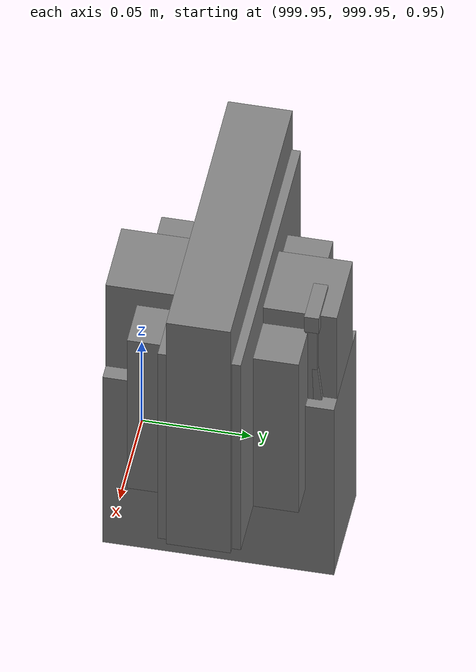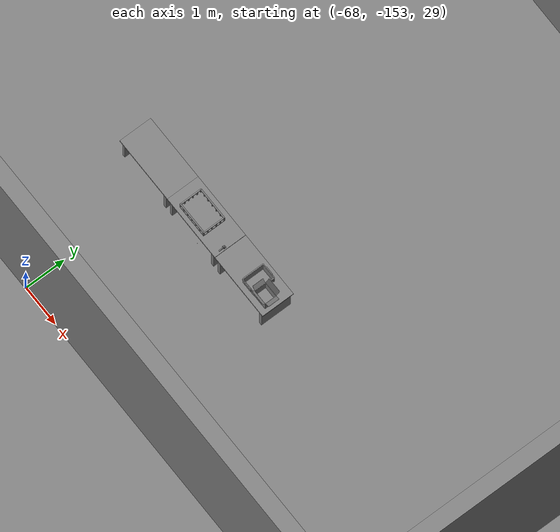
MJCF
<mujoco>
    <option gravity="0.000000000 0.000000000 -9.810000420" timestep="0.0049999999" integrator="implicitfast" density="1.225" viscosity="1.8000001e-05" noslip_iterations="10" iterations="100" sdf_iterations="50">
        <flag multiccd="disable"/>
    </option>
    <size memory="1000M"/>
    <compiler coordinate="local"/>
    <worldbody>
        <light cutoff="30" pos="0 1 1" dir="0 -1 -2"/>
        <light cutoff="30" pos="0 -1 1" dir="0 1 -2"/>
        <body pos="-64.866622925 -149.383972168 30.183746338" euler="89.999984741 89.999946594 0.000000000" name="openloong_gripper_2f85_fix_base_usda_bluebox_01">
            <geom contype="1" conaffinity="1" density="1000" type="box" material="" rgba="0.500000000 0.500000000 0.500000000 1.000000000" solimp="0.899999976 0.949999988 0.001000000" friction="1.000000000 0.005000000 0.000100000" solref="0.020000000 1.000000000" margin="0" condim="3" group="0" pos="0.276580811 0.187225342 0.000068665" quat="0.707106948 0.000077471 0.707106352 0.000077486" size="0.100000001 0.057999998 0.010000000" name="openloong_gripper_2f85_fix_base_usda_geom_17ADF606_FE45_4B37_B0AD_ADDCAADD7F85"/>
            <geom contype="1" conaffinity="1" density="1000" type="box" material="" rgba="0.500000000 0.500000000 0.500000000 1.000000000" solimp="0.899999976 0.949999988 0.001000000" friction="1.000000000 0.005000000 0.000100000" solref="0.020000000 1.000000000" margin="0" condim="3" group="0" pos="0.000000000 0.002883911 0.000000000" quat="0.999999881 0.000000000 0.000000000 0.000000000" size="0.254000008 0.003000000 0.172000006" name="openloong_gripper_2f85_fix_base_usda_geom_7C3DCD31_60CC_4973_9C39_DE1E4C236253"/>
            <geom contype="1" conaffinity="1" density="1000" type="box" material="" rgba="0.500000000 0.500000000 0.500000000 1.000000000" solimp="0.899999976 0.949999988 0.001000000" friction="1.000000000 0.005000000 0.000100000" solref="0.020000000 1.000000000" margin="0" condim="3" group="0" pos="0.000000000 0.124874115 0.173484802" quat="0.999796331 0.020176515 -0.000000015 0.000000030" size="0.259999990 0.119999997 0.007000000" name="openloong_gripper_2f85_fix_base_usda_geom_15D6FBD9_C200_437F_B8E5_D4AA9DE54273"/>
            <geom contype="1" conaffinity="1" density="1000" type="box" material="" rgba="0.500000000 0.500000000 0.500000000 1.000000000" solimp="0.899999976 0.949999988 0.001000000" friction="1.000000000 0.005000000 0.000100000" solref="0.020000000 1.000000000" margin="0" condim="3" group="0" pos="0.000000000 0.124874115 -0.173469543" quat="0.999796331 -0.020176545 -0.000000015 0.000000000" size="0.259999990 0.119999997 0.007000000" name="openloong_gripper_2f85_fix_base_usda_geom_F922DC4F_CEAF_466D_A86E_8C476D92B322"/>
            <geom contype="1" conaffinity="1" density="1000" type="box" material="" rgba="0.500000000 0.500000000 0.500000000 1.000000000" solimp="0.899999976 0.949999988 0.001000000" friction="1.000000000 0.005000000 0.000100000" solref="0.020000000 1.000000000" margin="0" condim="3" group="0" pos="0.000000000 0.214008331 0.188980103" quat="0.999912977 0.013176724 0.000000015 0.000000000" size="0.259999990 0.029999999 0.012500000" name="openloong_gripper_2f85_fix_base_usda_geom_8BDE61EA_DF06_4DD0_A9C6_E0511C363716"/>
            <geom contype="1" conaffinity="1" density="1000" type="box" material="" rgba="0.500000000 0.500000000 0.500000000 1.000000000" solimp="0.899999976 0.949999988 0.001000000" friction="1.000000000 0.005000000 0.000100000" solref="0.020000000 1.000000000" margin="0" condim="3" group="0" pos="-0.258361816 0.125289917 0.001876831" quat="0.702796936 -0.020792112 0.710783124 0.020769298" size="0.189999998 0.119999997 0.009000000" name="openloong_gripper_2f85_fix_base_usda_geom_20246941_3DA7_4027_AEB2_C4A097C7D2ED"/>
            <geom contype="1" conaffinity="1" density="1000" type="box" material="" rgba="0.500000000 0.500000000 0.500000000 1.000000000" solimp="0.899999976 0.949999988 0.001000000" friction="1.000000000 0.005000000 0.000100000" solref="0.020000000 1.000000000" margin="0" condim="3" group="0" pos="0.000000000 0.214008331 -0.188980103" quat="0.999912977 -0.013176769 0.000000030 0.000000015" size="0.259999990 0.029999999 0.012500000" name="openloong_gripper_2f85_fix_base_usda_geom_D006B487_A8FA_4EFD_9A19_7929F93F8945"/>
            <geom contype="1" conaffinity="1" density="1000" type="box" material="" rgba="0.500000000 0.500000000 0.500000000 1.000000000" solimp="0.899999976 0.949999988 0.001000000" friction="1.000000000 0.005000000 0.000100000" solref="0.020000000 1.000000000" margin="0" condim="3" group="0" pos="-0.276611328 0.187225342 0.000068665" quat="0.707106650 0.000077441 0.707106709 0.000077456" size="0.100000001 0.057999998 0.010000000" name="openloong_gripper_2f85_fix_base_usda_geom_3CF326D4_C9F3_4759_A414_C706FB15F079"/>
            <geom contype="1" conaffinity="1" density="1000" type="box" material="" rgba="0.500000000 0.500000000 0.500000000 1.000000000" solimp="0.899999976 0.949999988 0.001000000" friction="1.000000000 0.005000000 0.000100000" solref="0.020000000 1.000000000" margin="0" condim="3" group="0" pos="0.258331299 0.125289917 0.001876831" quat="0.702851415 0.018856421 0.710823774 -0.019329369" size="0.189999998 0.119999997 0.009000000" name="openloong_gripper_2f85_fix_base_usda_geom_DE6A8B9D_C4DD_46A8_B24D_361C53D6787D"/>
            <freejoint name="openloong_gripper_2f85_fix_base_usda_bluebox_01_joint"/>
            <site size="0.005000000 0.005000000 0.005000000" rgba="0.500000000 0.500000000 0.500000000 1.000000000" pos="0.000000000 0.000000000 0.000000000" quat="0.999961913 0.008726534 0.000000000 0.000000000" group="0" type="sphere" name="openloong_gripper_2f85_fix_base_usda_bluebox_01site"/>
        </body>
        <body pos="-64.496299744 -149.491867065 30.235729218" euler="0.000000000 0.000000000 89.999946594" name="openloong_gripper_2f85_fix_base_usda_cardboardbox_01">
            <geom contype="1" conaffinity="1" density="1000" type="box" material="" rgba="0.500000000 0.500000000 0.500000000 1.000000000" solimp="0.899999976 0.949999988 0.001000000" friction="1.000000000 0.005000000 0.000100000" solref="0.020000000 1.000000000" margin="0" condim="3" group="0" pos="-0.003166199 -0.004086494 0.005052090" quat="1.000000000 0.000000000 0.000000000 0.000000000" size="0.142499998 0.177500010 0.005000000" name="openloong_gripper_2f85_fix_base_usda_geom_CB9D456E_5588_4612_A040_D33829BE0995"/>
            <geom contype="1" conaffinity="1" density="1000" type="box" material="" rgba="0.500000000 0.500000000 0.500000000 1.000000000" solimp="0.899999976 0.949999988 0.001000000" friction="1.000000000 0.005000000 0.000100000" solref="0.020000000 1.000000000" margin="0" condim="3" group="0" pos="-0.003166199 0.170316696 0.150570869" quat="1.000000000 0.000000000 0.000000000 0.000000000" size="0.142499998 0.005000000 0.149999991" name="openloong_gripper_2f85_fix_base_usda_geom_F543424C_C142_4A5A_AFFD_E05C9CBA3B9A"/>
            <geom contype="1" conaffinity="1" density="1000" type="box" material="" rgba="0.500000000 0.500000000 0.500000000 1.000000000" solimp="0.899999976 0.949999988 0.001000000" friction="1.000000000 0.005000000 0.000100000" solref="0.020000000 1.000000000" margin="0" condim="3" group="0" pos="-0.147399902 -0.005307198 0.150570869" quat="1.000000000 0.000000000 0.000000000 0.000000000" size="0.005000000 0.177500010 0.149999991" name="openloong_gripper_2f85_fix_base_usda_geom_BE2B73BA_5D29_4B85_82E2_E01CA67B0DD7"/>
            <geom contype="1" conaffinity="1" density="1000" type="box" material="" rgba="0.500000000 0.500000000 0.500000000 1.000000000" solimp="0.899999976 0.949999988 0.001000000" friction="1.000000000 0.005000000 0.000100000" solref="0.020000000 1.000000000" margin="0" condim="3" group="0" pos="0.140275955 -0.005307198 0.150570869" quat="1.000000000 0.000000000 0.000000000 0.000000000" size="0.005000000 0.177500010 0.149999991" name="openloong_gripper_2f85_fix_base_usda_geom_452F41D1_85D9_48A4_ADE8_0EF94C7608A8"/>
            <geom contype="1" conaffinity="1" density="1000" type="box" material="" rgba="0.500000000 0.500000000 0.500000000 1.000000000" solimp="0.899999976 0.949999988 0.001000000" friction="1.000000000 0.005000000 0.000100000" solref="0.020000000 1.000000000" margin="0" condim="3" group="0" pos="-0.003166199 -0.181550980 0.150570869" quat="1.000000000 0.000000000 0.000000000 0.000000000" size="0.142499998 0.005000000 0.149999991" name="openloong_gripper_2f85_fix_base_usda_geom_0EDD7B79_C1FD_4BF1_A2E5_E9E223D8469D"/>
            <freejoint name="openloong_gripper_2f85_fix_base_usda_cardboardbox_01_joint"/>
            <site size="0.005000000 0.005000000 0.005000000" rgba="0.500000000 0.500000000 0.500000000 1.000000000" pos="0.000000000 0.000000000 0.000000000" quat="0.999961913 0.008726535 0.000000000 0.000000000" group="0" type="sphere" name="openloong_gripper_2f85_fix_base_usda_site_B5B47B9E_6FF9_4D5F_B6BA_86C18801693B"/>
            <body pos="0.139160156 -0.004048347 0.301930904" euler="-179.999954224 49.383502960 179.999954224" name="openloong_gripper_2f85_fix_base_usda_A1_006">
                <geom contype="1" conaffinity="1" density="1000" type="box" material="" rgba="0.500000000 0.500000000 0.500000000 1.000000000" solimp="0.899999976 0.949999988 0.001000000" friction="1.000000000 0.005000000 0.000100000" solref="0.020000000 1.000000000" margin="0" condim="3" group="0" pos="-0.071587563 0.000009537 0.001745224" quat="0.999999881 0.000000000 0.000000000 0.000000000" size="0.071249999 0.179999992 0.002500000" name="openloong_gripper_2f85_fix_base_usda_geom_F08B3DF7_13F6_41FA_9FE7_8636C8F87286"/>
                <joint armature="0" stiffness="0.07" damping="0.0099999998" axis="0.000000 1.000000 0.000000" type="hinge" name="openloong_gripper_2f85_fix_base_usda_A1_006"/>
            </body>
            <body pos="-0.145902634 -0.004086494 0.301938057" euler="-180.000000000 -60.000011444 -180.000000000" name="openloong_gripper_2f85_fix_base_usda_A2_006">
                <geom contype="1" conaffinity="1" density="1000" type="box" material="" rgba="0.500000000 0.500000000 0.500000000 1.000000000" solimp="0.899999976 0.949999988 0.001000000" friction="1.000000000 0.005000000 0.000100000" solref="0.020000000 1.000000000" margin="0" condim="3" group="0" pos="0.071268082 0.000009537 0.002717972" quat="0.000002921 0.000000000 -0.000000030 0.999999881" size="0.071249999 0.179999992 0.002500000" name="openloong_gripper_2f85_fix_base_usda_geom_D03F5E27_2B28_4687_9864_D35CE62CE317"/>
                <joint armature="0" stiffness="0.07" damping="0.0099999998" axis="0.000000 1.000000 0.000000" type="hinge" name="openloong_gripper_2f85_fix_base_usda_A2_006"/>
            </body>
            <body pos="-0.003385544 0.175991058 0.301930904" euler="-125.858116150 -0.000004561 0.000002331" name="openloong_gripper_2f85_fix_base_usda_B2_006">
                <geom contype="1" conaffinity="1" density="1000" type="box" material="" rgba="0.500000000 0.500000000 0.500000000 1.000000000" solimp="0.899999976 0.949999988 0.001000000" friction="1.000000000 0.005000000 0.000100000" solref="0.020000000 1.000000000" margin="0" condim="3" group="0" pos="0.000009537 -0.070939064 -0.002470016" quat="0.999614120 0.027776197 -0.000000015 0.000000030" size="0.137500003 0.064999998 0.005000000" name="openloong_gripper_2f85_fix_base_usda_geom_25EAB9E5_BAC8_4161_B774_C65D34FC571C"/>
                <joint armature="0" stiffness="0.07" damping="0.0099999998" axis="1.000000 0.000000 0.000000" type="hinge" name="openloong_gripper_2f85_fix_base_usda_B2_006"/>
            </body>
            <body pos="-0.003385544 -0.184140205 0.301938057" euler="147.805557251 0.000000000 0.000000000" name="openloong_gripper_2f85_fix_base_usda_B1_006">
                <geom contype="1" conaffinity="1" density="1000" type="box" material="" rgba="0.500000000 0.500000000 0.500000000 1.000000000" solimp="0.899999976 0.949999988 0.001000000" friction="1.000000000 0.005000000 0.000100000" solref="0.020000000 1.000000000" margin="0" condim="3" group="0" pos="-0.000028610 0.070202351 -0.002703667" quat="0.999614179 -0.027776167 0.000000000 0.000000000" size="0.137500003 0.064999998 0.005000000" name="openloong_gripper_2f85_fix_base_usda_geom_3E796E63_11A0_4BF0_8245_42D7A01C3A01"/>
                <joint armature="0" stiffness="0.07" damping="0.0099999998" axis="1.000000 0.000000 0.000000" type="hinge" name="openloong_gripper_2f85_fix_base_usda_B1_006"/>
            </body>
        </body>
        <body pos="-65.882858276 -149.481979370 30.229999542" euler="-64.487716675 0.000000000 0.000000000" name="openloong_gripper_2f85_fix_base_usda_Barcode">
            <geom contype="1" conaffinity="1" density="1000" type="box" material="" rgba="0.500000000 0.500000000 0.500000000 1.000000000" solimp="0.899999976 0.949999988 0.001000000" friction="1.000000000 0.005000000 0.000100000" solref="0.020000000 1.000000000" margin="0" condim="3" group="0" pos="0.000000000 0.013038635 0.001419067" quat="0.000000000 0.000000000 0.000000000 1.000000119" size="0.034000002 0.010000000 0.017999999" name="openloong_gripper_2f85_fix_base_usda_geom_C426BC76_3E25_41A1_BB0A_E1508CAD2F2D"/>
            <geom contype="1" conaffinity="1" density="1000" type="box" material="" rgba="0.500000000 0.500000000 0.500000000 1.000000000" solimp="0.899999976 0.949999988 0.001000000" friction="1.000000000 0.005000000 0.000100000" solref="0.020000000 1.000000000" margin="0" condim="3" group="0" pos="0.000000000 -0.035301208 -0.007095337" quat="0.000000000 0.000000000 -0.043619365 0.999048233" size="0.028999999 0.010000000 0.020000000" name="openloong_gripper_2f85_fix_base_usda_geom_6A1AB1E2_17A4_4274_AC52_15E6863233E8"/>
            <geom contype="1" conaffinity="1" density="1000" type="box" material="" rgba="0.500000000 0.500000000 0.500000000 1.000000000" solimp="0.899999976 0.949999988 0.001000000" friction="1.000000000 0.005000000 0.000100000" solref="0.020000000 1.000000000" margin="0" condim="3" group="0" pos="0.000000000 -0.043411255 -0.011749268" quat="0.922262907 0.386563420 0.000000000 0.000000000" size="0.026000001 0.010000000 0.020000000" name="openloong_gripper_2f85_fix_base_usda_geom_0238AC73_8613_43FA_A5BE_5D940589E8EA"/>
            <geom contype="1" conaffinity="1" density="1000" type="box" material="" rgba="0.500000000 0.500000000 0.500000000 1.000000000" solimp="0.899999976 0.949999988 0.001000000" friction="1.000000000 0.005000000 0.000100000" solref="0.020000000 1.000000000" margin="0" condim="3" group="0" pos="0.000000000 -0.016967773 -0.031860352" quat="0.000000000 0.000000000 0.000000000 1.000000119" size="0.008000000 0.010000000 0.013000000" name="openloong_gripper_2f85_fix_base_usda_geom_1DCD4803_6513_4206_AE24_862078D75F53"/>
            <geom contype="1" conaffinity="1" density="1000" type="box" material="" rgba="0.500000000 0.500000000 0.500000000 1.000000000" solimp="0.899999976 0.949999988 0.001000000" friction="1.000000000 0.005000000 0.000100000" solref="0.020000000 1.000000000" margin="0" condim="3" group="0" pos="0.000000000 -0.001869202 0.000312805" quat="0.953716993 0.300705761 0.000000000 0.000000000" size="0.032000002 0.010000000 0.018999999" name="openloong_gripper_2f85_fix_base_usda_geom_F76E4BA0_F594_4DC9_B5DB_F5F28664CE4C"/>
            <geom contype="1" conaffinity="1" density="1000" type="box" material="" rgba="0.500000000 0.500000000 0.500000000 1.000000000" solimp="0.899999976 0.949999988 0.001000000" friction="1.000000000 0.005000000 0.000100000" solref="0.020000000 1.000000000" margin="0" condim="3" group="0" pos="0.000000000 -0.019531250 -0.003173828" quat="0.953716993 0.300705761 0.000000000 0.000000000" size="0.030999999 0.010000000 0.020000000" name="openloong_gripper_2f85_fix_base_usda_geom_E72D1D47_8DAF_4CDE_8B0F_4E24390AF188"/>
            <geom contype="1" conaffinity="1" density="1000" type="box" material="" rgba="0.500000000 0.500000000 0.500000000 1.000000000" solimp="0.899999976 0.949999988 0.001000000" friction="1.000000000 0.005000000 0.000100000" solref="0.020000000 1.000000000" margin="0" condim="3" group="0" pos="0.000000000 -0.035301208 -0.007095337" quat="0.953716993 0.300705761 0.000000000 0.000000000" size="0.028999999 0.010000000 0.020000000" name="openloong_gripper_2f85_fix_base_usda_geom_FE0D1756_034D_490E_8AF5_429024AFDB56"/>
            <geom contype="1" conaffinity="1" density="1000" type="box" material="" rgba="0.500000000 0.500000000 0.500000000 1.000000000" solimp="0.899999976 0.949999988 0.001000000" friction="1.000000000 0.005000000 0.000100000" solref="0.020000000 1.000000000" margin="0" condim="3" group="0" pos="0.000000000 -0.042617798 -0.071121216" quat="0.000000000 0.000000000 0.000000000 1.000000119" size="0.013000000 0.021000000 0.059999999" name="openloong_gripper_2f85_fix_base_usda_geom_4B3702B4_384B_4AA0_88F9_924A2C0FB193"/>
            <freejoint name="openloong_gripper_2f85_fix_base_usda_Barcode_joint"/>
            <site size="0.005000000 0.005000000 0.005000000" rgba="0.500000000 0.500000000 0.500000000 1.000000000" pos="0.000000000 0.000000000 0.000000000" quat="1.000000000 0.000000000 0.000000000 0.000000000" group="0" type="sphere" name="openloong_gripper_2f85_fix_base_usda_Barcode_site"/>
        </body>
        <body pos="-66.745018005 -149.392349243 30.184000015" euler="0.000000000 0.000000000 89.999946594" name="[22329852463342]_Basket_01">
            <geom contype="1" conaffinity="1" density="1000" type="box" material="" rgba="0.500000000 0.500000000 0.500000000 1.000000000" solimp="0.899999976 0.949999988 0.001000000" friction="1.000000000 0.005000000 0.000100000" solref="0.020000000 1.000000000" margin="0" condim="3" group="0" pos="-0.052425385 0.389207840 0.089787483" quat="0.707107008 0.000000000 0.000000000 0.707106411" size="0.014249999 0.014249999 0.059999999" name="[22329852463342]_geom_58E23BF8_4508_4754_990B_9A7E0DA5CBFD"/>
            <geom contype="1" conaffinity="1" density="1000" type="box" material="" rgba="0.500000000 0.500000000 0.500000000 1.000000000" solimp="0.899999976 0.949999988 0.001000000" friction="1.000000000 0.005000000 0.000100000" solref="0.020000000 1.000000000" margin="0" condim="3" group="0" pos="0.264015198 -0.133043289 0.089787483" quat="0.707107008 0.000000000 0.000000000 0.707106411" size="0.014249999 0.014249999 0.059999999" name="[22329852463342]_geom_C4E14F77_D3A3_400B_AD11_502E8D24639C"/>
            <geom contype="1" conaffinity="1" density="1000" type="box" material="" rgba="0.500000000 0.500000000 0.500000000 1.000000000" solimp="0.899999976 0.949999988 0.001000000" friction="1.000000000 0.005000000 0.000100000" solref="0.020000000 1.000000000" margin="0" condim="3" group="0" pos="-0.264015198 -0.265548706 0.089793205" quat="0.707107008 0.000000000 0.000000000 0.707106411" size="0.014249999 0.014249999 0.059999999" name="[22329852463342]_geom_86954375_4D74_41F7_9EC0_5C2FB41AB599"/>
            <geom contype="1" conaffinity="1" density="1000" type="box" material="" rgba="0.500000000 0.500000000 0.500000000 1.000000000" solimp="0.899999976 0.949999988 0.001000000" friction="1.000000000 0.005000000 0.000100000" solref="0.020000000 1.000000000" margin="0" condim="3" group="0" pos="-0.160263062 -0.389322281 0.089793205" quat="0.707107008 0.000000000 0.000000000 0.707106411" size="0.014249999 0.014249999 0.059999999" name="[22329852463342]_geom_B258E742_0C6E_4FE7_8DBC_0196A7456435"/>
            <geom contype="1" conaffinity="1" density="1000" type="box" material="" rgba="0.500000000 0.500000000 0.500000000 1.000000000" solimp="0.899999976 0.949999988 0.001000000" friction="1.000000000 0.005000000 0.000100000" solref="0.020000000 1.000000000" margin="0" condim="3" group="0" pos="0.162265778 -0.389322281 0.089787483" quat="0.707107008 0.000000000 0.000000000 0.707106411" size="0.014249999 0.014249999 0.059999999" name="[22329852463342]_geom_0E432CEA_D270_4409_A66E_D5E22444F87B"/>
            <geom contype="1" conaffinity="1" density="1000" type="box" material="" rgba="0.500000000 0.500000000 0.500000000 1.000000000" solimp="0.899999976 0.949999988 0.001000000" friction="1.000000000 0.005000000 0.000100000" solref="0.020000000 1.000000000" margin="0" condim="3" group="0" pos="0.264015198 0.389207840 0.089787483" quat="0.707107008 0.000000000 0.000000000 0.707106411" size="0.014249999 0.014249999 0.059999999" name="[22329852463342]_geom_BCC0D29F_04F3_42FB_8C36_B62A238F1977"/>
            <geom contype="1" conaffinity="1" density="1000" type="box" material="" rgba="0.500000000 0.500000000 0.500000000 1.000000000" solimp="0.899999976 0.949999988 0.001000000" friction="1.000000000 0.005000000 0.000100000" solref="0.020000000 1.000000000" margin="0" condim="3" group="0" pos="-0.264015198 -0.133043289 0.089793205" quat="0.707107008 0.000000000 0.000000000 0.707106411" size="0.014249999 0.014249999 0.059999999" name="[22329852463342]_geom_842C3D8E_7210_46CF_ADF2_43D8E37E4632"/>
            <geom contype="1" conaffinity="1" density="1000" type="box" material="" rgba="0.500000000 0.500000000 0.500000000 1.000000000" solimp="0.899999976 0.949999988 0.001000000" friction="1.000000000 0.005000000 0.000100000" solref="0.020000000 1.000000000" margin="0" condim="3" group="0" pos="-0.264026642 0.269256592 0.089793205" quat="0.707107008 0.000000000 0.000000000 0.707106411" size="0.014249999 0.014249999 0.059999999" name="[22329852463342]_geom_B814D7C7_223E_4648_BAE0_9D9558413F2B"/>
            <geom contype="1" conaffinity="1" density="1000" type="box" material="" rgba="0.500000000 0.500000000 0.500000000 1.000000000" solimp="0.899999976 0.949999988 0.001000000" friction="1.000000000 0.005000000 0.000100000" solref="0.020000000 1.000000000" margin="0" condim="3" group="0" pos="0.054462433 0.389207840 0.089787483" quat="0.707107008 0.000000000 0.000000000 0.707106411" size="0.014249999 0.014249999 0.059999999" name="[22329852463342]_geom_7ED5666E_45CA_4546_B347_2080A0A1FE51"/>
            <geom contype="1" conaffinity="1" density="1000" type="box" material="" rgba="0.500000000 0.500000000 0.500000000 1.000000000" solimp="0.899999976 0.949999988 0.001000000" friction="1.000000000 0.005000000 0.000100000" solref="0.020000000 1.000000000" margin="0" condim="3" group="0" pos="0.054462433 -0.389322281 0.089787483" quat="0.707107008 0.000000000 0.000000000 0.707106411" size="0.014249999 0.014249999 0.059999999" name="[22329852463342]_geom_11991B22_B068_42FF_8281_ABBF3A197132"/>
            <geom contype="1" conaffinity="1" density="1000" type="box" material="" rgba="0.500000000 0.500000000 0.500000000 1.000000000" solimp="0.899999976 0.949999988 0.001000000" friction="1.000000000 0.005000000 0.000100000" solref="0.020000000 1.000000000" margin="0" condim="3" group="0" pos="0.264015198 0.269256592 0.089793205" quat="0.707107008 0.000000000 0.000000000 0.707106411" size="0.014249999 0.014249999 0.059999999" name="[22329852463342]_geom_93D96DBB_32BF_4AD8_8619_A1B0141C2641"/>
            <geom contype="1" conaffinity="1" density="1000" type="box" material="" rgba="0.500000000 0.500000000 0.500000000 1.000000000" solimp="0.899999976 0.949999988 0.001000000" friction="1.000000000 0.005000000 0.000100000" solref="0.020000000 1.000000000" margin="0" condim="3" group="0" pos="0.264015198 -0.389322281 0.089787483" quat="0.707107008 0.000000000 0.000000000 0.707106411" size="0.014249999 0.014249999 0.059999999" name="[22329852463342]_geom_23BDB4C5_E02F_4187_9089_841130DD4DD9"/>
            <geom contype="1" conaffinity="1" density="1000" type="box" material="" rgba="0.500000000 0.500000000 0.500000000 1.000000000" solimp="0.899999976 0.949999988 0.001000000" friction="1.000000000 0.005000000 0.000100000" solref="0.020000000 1.000000000" margin="0" condim="3" group="0" pos="0.000000000 0.000000000 0.015998840" quat="0.707107008 0.000000000 0.000000000 0.707106411" size="0.403499991 0.279000014 0.015750000" name="[22329852463342]_geom_F91212DB_7EBB_4662_8D26_7A67BAF2ED6C"/>
            <geom contype="1" conaffinity="1" density="1000" type="box" material="" rgba="0.500000000 0.500000000 0.500000000 1.000000000" solimp="0.899999976 0.949999988 0.001000000" friction="1.000000000 0.005000000 0.000100000" solref="0.020000000 1.000000000" margin="0" condim="3" group="0" pos="0.000000000 -0.389476776 0.163619041" quat="0.707107008 0.000000000 0.000000000 0.707106411" size="0.015000000 0.277500004 0.015750000" name="[22329852463342]_geom_24737E70_D0D4_41F2_8FA0_206D1DFCB79F"/>
            <geom contype="1" conaffinity="1" density="1000" type="box" material="" rgba="0.500000000 0.500000000 0.500000000 1.000000000" solimp="0.899999976 0.949999988 0.001000000" friction="1.000000000 0.005000000 0.000100000" solref="0.020000000 1.000000000" margin="0" condim="3" group="0" pos="0.162265778 0.389207840 0.089787483" quat="0.707107008 0.000000000 0.000000000 0.707106411" size="0.014249999 0.014249999 0.059999999" name="[22329852463342]_geom_C35F0FE6_C692_4B99_988A_93D73DCA490B"/>
            <geom contype="1" conaffinity="1" density="1000" type="box" material="" rgba="0.500000000 0.500000000 0.500000000 1.000000000" solimp="0.899999976 0.949999988 0.001000000" friction="1.000000000 0.005000000 0.000100000" solref="0.020000000 1.000000000" margin="0" condim="3" group="0" pos="0.000000000 0.389471054 0.163619041" quat="0.707107008 0.000000000 0.000000000 0.707106411" size="0.015000000 0.277500004 0.015750000" name="[22329852463342]_geom_7495F6BF_BDF8_4E16_BF6C_6EAC3411EA06"/>
            <geom contype="1" conaffinity="1" density="1000" type="box" material="" rgba="0.500000000 0.500000000 0.500000000 1.000000000" solimp="0.899999976 0.949999988 0.001000000" friction="1.000000000 0.005000000 0.000100000" solref="0.020000000 1.000000000" margin="0" condim="3" group="0" pos="-0.263511658 0.000000000 0.163619041" quat="0.707107008 0.000000000 0.000000000 0.707106411" size="0.403499991 0.015000000 0.015750000" name="[22329852463342]_geom_F04C2C0B_A972_4319_A90F_ED31C0D96727"/>
            <geom contype="1" conaffinity="1" density="1000" type="box" material="" rgba="0.500000000 0.500000000 0.500000000 1.000000000" solimp="0.899999976 0.949999988 0.001000000" friction="1.000000000 0.005000000 0.000100000" solref="0.020000000 1.000000000" margin="0" condim="3" group="0" pos="-0.264015198 0.141334534 0.089793205" quat="0.707107008 0.000000000 0.000000000 0.707106411" size="0.014249999 0.014249999 0.059999999" name="[22329852463342]_geom_ED36C04B_3E2B_4C59_B00B_7EC2BDE99ACC"/>
            <geom contype="1" conaffinity="1" density="1000" type="box" material="" rgba="0.500000000 0.500000000 0.500000000 1.000000000" solimp="0.899999976 0.949999988 0.001000000" friction="1.000000000 0.005000000 0.000100000" solref="0.020000000 1.000000000" margin="0" condim="3" group="0" pos="0.264015198 -0.265548706 0.089787483" quat="0.707107008 0.000000000 0.000000000 0.707106411" size="0.014249999 0.014249999 0.059999999" name="[22329852463342]_geom_4C2737DC_D122_4B20_9BE6_13CC0AF58ABB"/>
            <geom contype="1" conaffinity="1" density="1000" type="box" material="" rgba="0.500000000 0.500000000 0.500000000 1.000000000" solimp="0.899999976 0.949999988 0.001000000" friction="1.000000000 0.005000000 0.000100000" solref="0.020000000 1.000000000" margin="0" condim="3" group="0" pos="-0.160263062 0.389207840 0.089787483" quat="0.707107008 0.000000000 0.000000000 0.707106411" size="0.014249999 0.014249999 0.059999999" name="[22329852463342]_geom_15283FFD_292C_410F_A56F_A66868D0FC5C"/>
            <geom contype="1" conaffinity="1" density="1000" type="box" material="" rgba="0.500000000 0.500000000 0.500000000 1.000000000" solimp="0.899999976 0.949999988 0.001000000" friction="1.000000000 0.005000000 0.000100000" solref="0.020000000 1.000000000" margin="0" condim="3" group="0" pos="-0.052425385 -0.389322281 0.089787483" quat="0.707107008 0.000000000 0.000000000 0.707106411" size="0.014249999 0.014249999 0.059999999" name="[22329852463342]_geom_3549ED5B_4F47_44AA_B986_D40B4D26D053"/>
            <geom contype="1" conaffinity="1" density="1000" type="box" material="" rgba="0.500000000 0.500000000 0.500000000 1.000000000" solimp="0.899999976 0.949999988 0.001000000" friction="1.000000000 0.005000000 0.000100000" solref="0.020000000 1.000000000" margin="0" condim="3" group="0" pos="-0.264026642 -0.389322281 0.089793205" quat="0.707107008 0.000000000 0.000000000 0.707106411" size="0.014249999 0.014249999 0.059999999" name="[22329852463342]_geom_03458A1A_FC1B_48AC_9BE0_A606B2D3E5C2"/>
            <geom contype="1" conaffinity="1" density="1000" type="box" material="" rgba="0.500000000 0.500000000 0.500000000 1.000000000" solimp="0.899999976 0.949999988 0.001000000" friction="1.000000000 0.005000000 0.000100000" solref="0.020000000 1.000000000" margin="0" condim="3" group="0" pos="0.264015198 0.141334534 0.089787483" quat="0.707107008 0.000000000 0.000000000 0.707106411" size="0.014249999 0.014249999 0.059999999" name="[22329852463342]_geom_1EB8E2BE_D0A2_46AC_9EC2_1DBFFFAEC3CF"/>
            <geom contype="1" conaffinity="1" density="1000" type="box" material="" rgba="0.500000000 0.500000000 0.500000000 1.000000000" solimp="0.899999976 0.949999988 0.001000000" friction="1.000000000 0.005000000 0.000100000" solref="0.020000000 1.000000000" margin="0" condim="3" group="0" pos="-0.264015198 0.389207840 0.089793205" quat="0.707107008 0.000000000 0.000000000 0.707106411" size="0.014249999 0.014249999 0.059999999" name="[22329852463342]_geom_C1B07EC1_6B05_48E8_B31C_33B1D55641E8"/>
            <geom contype="1" conaffinity="1" density="1000" type="box" material="" rgba="0.500000000 0.500000000 0.500000000 1.000000000" solimp="0.899999976 0.949999988 0.001000000" friction="1.000000000 0.005000000 0.000100000" solref="0.020000000 1.000000000" margin="0" condim="3" group="0" pos="0.264015198 0.004480362 0.089787483" quat="0.707107008 0.000000000 0.000000000 0.707106411" size="0.014249999 0.014249999 0.059999999" name="[22329852463342]_geom_F3F3C037_C3CA_4468_80A0_193222CE52F4"/>
            <geom contype="1" conaffinity="1" density="1000" type="box" material="" rgba="0.500000000 0.500000000 0.500000000 1.000000000" solimp="0.899999976 0.949999988 0.001000000" friction="1.000000000 0.005000000 0.000100000" solref="0.020000000 1.000000000" margin="0" condim="3" group="0" pos="0.263694763 -0.000011444 0.163619041" quat="0.707107008 0.000000000 0.000000000 0.707106411" size="0.403499991 0.015000000 0.015750000" name="[22329852463342]_geom_C289E98E_3C0B_479F_8470_E36D198798B5"/>
            <geom contype="1" conaffinity="1" density="1000" type="box" material="" rgba="0.500000000 0.500000000 0.500000000 1.000000000" solimp="0.899999976 0.949999988 0.001000000" friction="1.000000000 0.005000000 0.000100000" solref="0.020000000 1.000000000" margin="0" condim="3" group="0" pos="-0.264015198 0.004480362 0.089793205" quat="0.707107008 0.000000000 0.000000000 0.707106411" size="0.014249999 0.014249999 0.059999999" name="[22329852463342]_geom_2F3255EB_0E11_46B5_B2B6_C29465E239C5"/>
            <freejoint name="[22329852463342]_joint_9D23F923_BC87_4086_A485_D2B6E97186E2"/>
        </body>
        <body pos="0.000000000 0.000000000 0.000000000" euler="0.000000000 0.000000000 0.000000000" name="Static Objects_Static Objects">
            <geom contype="1" conaffinity="1" density="1000" type="box" material="" rgba="0.500000000 0.500000000 0.500000000 1.000000000" solimp="0.899999976 0.949999988 0.001000000" friction="1.000000000 0.005000000 0.000100000" solref="0.020000000 1.000000000" margin="0" condim="3" group="0" pos="-67.544113159 -149.365814209 29.727830887" quat="0.500000417 0.499999970 0.499999553 0.499999970" size="0.381000012 0.319999993 0.041000001" name="Static Objects_geom_5CD316DE_AF9A_459A_88BB_335D3AD53733"/>
            <geom contype="1" conaffinity="1" density="1000" type="box" material="" rgba="0.500000000 0.500000000 0.500000000 1.000000000" solimp="0.899999976 0.949999988 0.001000000" friction="1.000000000 0.005000000 0.000100000" solref="0.020000000 1.000000000" margin="0" condim="3" group="0" pos="-68.239501953 -149.365814209 30.086868286" quat="0.500000417 0.499999970 0.499999553 0.499999970" size="0.370999992 0.039500002 0.745000005" name="Static Objects_geom_EABA7A63_3114_44C3_953F_B2DD48390049"/>
            <geom contype="1" conaffinity="1" density="1000" type="box" material="" rgba="0.500000000 0.500000000 0.500000000 1.000000000" solimp="0.899999976 0.949999988 0.001000000" friction="1.000000000 0.005000000 0.000100000" solref="0.020000000 1.000000000" margin="0" condim="3" group="0" pos="-68.239501953 -149.365814209 30.147235870" quat="0.500000417 0.499999970 0.499999553 0.499999970" size="0.400000006 0.022000000 0.800000012" name="Static Objects_geom_65F28E0B_4DF2_4021_8A8F_F3606416F155"/>
            <geom contype="1" conaffinity="1" density="1000" type="box" material="" rgba="0.500000000 0.500000000 0.500000000 1.000000000" solimp="0.899999976 0.949999988 0.001000000" friction="1.000000000 0.005000000 0.000100000" solref="0.020000000 1.000000000" margin="0" condim="3" group="0" pos="-68.934890747 -149.365814209 29.727830887" quat="0.500000417 0.499999970 0.499999553 0.499999970" size="0.381000012 0.319999993 0.041000001" name="Static Objects_geom_B6EA39D5_C6FA_45D1_B10C_2F62E10B6677"/>
            <geom contype="1" conaffinity="1" density="1000" type="box" material="" rgba="0.500000000 0.500000000 0.500000000 1.000000000" solimp="0.899999976 0.949999988 0.001000000" friction="1.000000000 0.005000000 0.000100000" solref="0.020000000 1.000000000" margin="0" condim="3" group="0" pos="-68.239501953 -149.365814209 29.561563492" quat="0.500000417 0.499999970 0.499999553 0.499999970" size="0.020000000 0.022000000 0.660000026" name="Static Objects_geom_E10D6489_CB48_4DF1_BC6B_940905906157"/>
            <geom contype="1" conaffinity="1" density="1000" type="box" material="" rgba="0.500000000 0.500000000 0.500000000 1.000000000" solimp="0.899999976 0.949999988 0.001000000" friction="1.000000000 0.005000000 0.000100000" solref="0.020000000 1.000000000" margin="0" condim="3" group="0" pos="-65.945671082 -149.365814209 29.727830887" quat="0.500000417 0.499999970 0.499999553 0.499999970" size="0.381000012 0.319999993 0.041000001" name="Static Objects_geom_46F6C31A_A5ED_4DFB_A5A6_C267DFC18ADD"/>
            <geom contype="1" conaffinity="1" density="1000" type="box" material="" rgba="0.500000000 0.500000000 0.500000000 1.000000000" solimp="0.899999976 0.949999988 0.001000000" friction="1.000000000 0.005000000 0.000100000" solref="0.020000000 1.000000000" margin="0" condim="3" group="0" pos="-66.641059875 -149.365814209 30.086868286" quat="0.500000417 0.499999970 0.499999553 0.499999970" size="0.370999992 0.039500002 0.745000005" name="Static Objects_geom_137379CD_2B55_491E_A486_8D37C7FD9D7B"/>
            <geom contype="1" conaffinity="1" density="1000" type="box" material="" rgba="0.500000000 0.500000000 0.500000000 1.000000000" solimp="0.899999976 0.949999988 0.001000000" friction="1.000000000 0.005000000 0.000100000" solref="0.020000000 1.000000000" margin="0" condim="3" group="0" pos="-66.641059875 -149.365814209 30.147235870" quat="0.500000417 0.499999970 0.499999553 0.499999970" size="0.400000006 0.022000000 0.800000012" name="Static Objects_geom_5FCB2133_28E2_401B_9BE8_D6B50878608B"/>
            <geom contype="1" conaffinity="1" density="1000" type="box" material="" rgba="0.500000000 0.500000000 0.500000000 1.000000000" solimp="0.899999976 0.949999988 0.001000000" friction="1.000000000 0.005000000 0.000100000" solref="0.020000000 1.000000000" margin="0" condim="3" group="0" pos="-67.336448669 -149.365814209 29.727830887" quat="0.500000417 0.499999970 0.499999553 0.499999970" size="0.381000012 0.319999993 0.041000001" name="Static Objects_geom_62790981_568B_44A3_9D4F_AE321B6771D9"/>
            <geom contype="1" conaffinity="1" density="1000" type="box" material="" rgba="0.500000000 0.500000000 0.500000000 1.000000000" solimp="0.899999976 0.949999988 0.001000000" friction="1.000000000 0.005000000 0.000100000" solref="0.020000000 1.000000000" margin="0" condim="3" group="0" pos="-66.641059875 -149.365814209 29.561563492" quat="0.500000417 0.499999970 0.499999553 0.499999970" size="0.020000000 0.022000000 0.660000026" name="Static Objects_geom_9041B9B4_F51A_442C_ADF7_6178BC60DA6A"/>
            <geom contype="1" conaffinity="1" density="1000" type="box" material="" rgba="0.500000000 0.500000000 0.500000000 1.000000000" solimp="0.899999976 0.949999988 0.001000000" friction="1.000000000 0.005000000 0.000100000" solref="0.020000000 1.000000000" margin="0" condim="3" group="0" pos="-64.338577271 -149.365814209 29.727830887" quat="0.500000417 0.499999970 0.499999553 0.499999970" size="0.381000012 0.319999993 0.041000001" name="Static Objects_geom_7F2BE2C3_E819_474D_8F28_2BA92C97A49A"/>
            <geom contype="1" conaffinity="1" density="1000" type="box" material="" rgba="0.500000000 0.500000000 0.500000000 1.000000000" solimp="0.899999976 0.949999988 0.001000000" friction="1.000000000 0.005000000 0.000100000" solref="0.020000000 1.000000000" margin="0" condim="3" group="0" pos="-65.033966064 -149.365814209 30.086868286" quat="0.500000417 0.499999970 0.499999553 0.499999970" size="0.370999992 0.039500002 0.745000005" name="Static Objects_geom_A71C927D_809A_44D7_8920_208D706C360E"/>
            <geom contype="1" conaffinity="1" density="1000" type="box" material="" rgba="0.500000000 0.500000000 0.500000000 1.000000000" solimp="0.899999976 0.949999988 0.001000000" friction="1.000000000 0.005000000 0.000100000" solref="0.020000000 1.000000000" margin="0" condim="3" group="0" pos="-65.033966064 -149.365814209 30.147235870" quat="0.500000417 0.499999970 0.499999553 0.499999970" size="0.400000006 0.022000000 0.800000012" name="Static Objects_geom_9AEBB5CB_4BA4_43E9_9C0B_67EED5136398"/>
            <geom contype="1" conaffinity="1" density="1000" type="box" material="" rgba="0.500000000 0.500000000 0.500000000 1.000000000" solimp="0.899999976 0.949999988 0.001000000" friction="1.000000000 0.005000000 0.000100000" solref="0.020000000 1.000000000" margin="0" condim="3" group="0" pos="-65.729354858 -149.365814209 29.727830887" quat="0.500000417 0.499999970 0.499999553 0.499999970" size="0.381000012 0.319999993 0.041000001" name="Static Objects_geom_85E38DA4_5E37_4A09_B264_B9948E484885"/>
            <geom contype="1" conaffinity="1" density="1000" type="box" material="" rgba="0.500000000 0.500000000 0.500000000 1.000000000" solimp="0.899999976 0.949999988 0.001000000" friction="1.000000000 0.005000000 0.000100000" solref="0.020000000 1.000000000" margin="0" condim="3" group="0" pos="-65.033966064 -149.365814209 29.561563492" quat="0.500000417 0.499999970 0.499999553 0.499999970" size="0.020000000 0.022000000 0.660000026" name="Static Objects_geom_22B06085_122D_4DB1_A9E5_AF80DFE52E73"/>
            <geom contype="1" conaffinity="1" density="1000" type="box" material="" rgba="0.500000000 0.500000000 0.500000000 1.000000000" solimp="0.899999976 0.949999988 0.001000000" friction="1.000000000 0.005000000 0.000100000" solref="0.020000000 1.000000000" margin="0" condim="3" group="0" pos="-61.754566193 -137.853729248 33.906845093" quat="0.707107067 0.000000000 0.000000000 0.707106471" size="0.759999990 0.759999990 4.500000000" name="Static Objects_geom_31933452_CFDC_4D41_A10A_72AA2D83CB52"/>
            <geom contype="1" conaffinity="1" density="1000" type="box" material="" rgba="0.500000000 0.500000000 0.500000000 1.000000000" solimp="0.899999976 0.949999988 0.001000000" friction="1.000000000 0.005000000 0.000100000" solref="0.020000000 1.000000000" margin="0" condim="3" group="0" pos="-57.511135101 -144.927108765 31.707921982" quat="1.000000000 0.000000000 0.000000000 0.000000000" size="0.200000003 8.000000000 2.299999952" name="Static Objects_geom_18147C93_44B9_430B_BAAA_AB27C7B7C5A0"/>
            <geom contype="1" conaffinity="1" density="1000" type="box" material="" rgba="0.500000000 0.500000000 0.500000000 1.000000000" solimp="0.899999976 0.949999988 0.001000000" friction="1.000000000 0.005000000 0.000100000" solref="0.020000000 1.000000000" margin="0" condim="3" group="0" pos="-80.517646790 -157.574050903 31.688196182" quat="0.707107067 0.000000000 0.000000000 0.707106471" size="0.600000024 0.600000024 2.299999952" name="Static Objects_geom_27A0E834_DC11_40A7_82AE_2C4EA5C6C350"/>
            <geom contype="1" conaffinity="1" density="1000" type="box" material="" rgba="0.500000000 0.500000000 0.500000000 1.000000000" solimp="0.899999976 0.949999988 0.001000000" friction="1.000000000 0.005000000 0.000100000" solref="0.020000000 1.000000000" margin="0" condim="3" group="0" pos="-80.711044312 -147.414932251 31.666158676" quat="1.000000000 0.000000000 0.000000000 0.000000000" size="0.200000003 10.000000000 2.299999952" name="Static Objects_geom_ED3DF20A_E76D_4D68_AE68_74B7F40CBC60"/>
            <geom contype="1" conaffinity="1" density="1000" type="box" material="" rgba="0.500000000 0.500000000 0.500000000 1.000000000" solimp="0.899999976 0.949999988 0.001000000" friction="1.000000000 0.005000000 0.000100000" solref="0.020000000 1.000000000" margin="0" condim="3" group="0" pos="-57.687217712 -137.434692383 31.688196182" quat="0.707107067 0.000000000 0.000000000 0.707106471" size="0.600000024 0.600000024 2.299999952" name="Static Objects_geom_CB387A1F_16DB_4A47_BFC3_265387FAFAE4"/>
            <geom contype="1" conaffinity="1" density="1000" type="box" material="" rgba="0.500000000 0.500000000 0.500000000 1.000000000" solimp="0.899999976 0.949999988 0.001000000" friction="1.000000000 0.005000000 0.000100000" solref="0.020000000 1.000000000" margin="0" condim="3" group="0" pos="-69.537033081 -140.263229370 31.714921951" quat="0.707107067 0.000000000 0.000000000 0.707106471" size="0.759999990 4.500000000 2.299999952" name="Static Objects_geom_3E22FF38_3B01_4B83_995E_B757A2080AA4"/>
            <geom contype="1" conaffinity="1" density="1000" type="box" material="" rgba="0.500000000 0.500000000 0.500000000 1.000000000" solimp="0.899999976 0.949999988 0.001000000" friction="1.000000000 0.005000000 0.000100000" solref="0.020000000 1.000000000" margin="0" condim="3" group="0" pos="-80.073638916 -137.853713989 33.906845093" quat="0.707107067 0.000000000 0.000000000 0.707106471" size="0.759999990 0.759999990 4.500000000" name="Static Objects_geom_ED88BE0F_214E_4986_81BC_40C50E0BAE1C"/>
            <geom contype="1" conaffinity="1" density="1000" type="box" material="" rgba="0.500000000 0.500000000 0.500000000 1.000000000" solimp="0.899999976 0.949999988 0.001000000" friction="1.000000000 0.005000000 0.000100000" solref="0.020000000 1.000000000" margin="0" condim="3" group="0" pos="-73.406707764 -155.734664917 31.707921982" quat="1.000000000 0.000000000 0.000000000 0.000000000" size="0.200000003 3.000000000 2.299999952" name="Static Objects_geom_EFB5C7A0_E658_41CD_BBD6_37FFD7569880"/>
            <geom contype="1" conaffinity="1" density="1000" type="box" material="" rgba="0.500000000 0.500000000 0.500000000 1.000000000" solimp="0.899999976 0.949999988 0.001000000" friction="1.000000000 0.005000000 0.000100000" solref="0.020000000 1.000000000" margin="0" condim="3" group="0" pos="-68.497543335 -137.448257446 31.707921982" quat="0.707107067 0.000000000 0.000000000 0.707106471" size="0.200000003 14.000000000 2.299999952" name="Static Objects_geom_5FAA26D7_778A_462F_9AF6_5748124F80AC"/>
            <geom contype="1" conaffinity="1" density="1000" type="cylinder" material="" rgba="0.500000000 0.500000000 0.500000000 1.000000000" solimp="0.899999976 0.949999988 0.001000000" friction="1.000000000 0.005000000 0.000100000" solref="0.020000000 1.000000000" margin="0" condim="3" group="0" pos="-68.868522644 -142.134506226 31.711090088" quat="0.707107067 0.000000000 0.000000000 0.707106471" size="0.509999990 2.299999952 1.000000000" name="Static Objects_geom_19B616D0_3AD6_4206_B55C_A06F8AC3E951"/>
            <geom contype="1" conaffinity="1" density="1000" type="plane" material="" rgba="0.500000000 0.500000000 0.500000000 1.000000000" solimp="0.899999976 0.949999988 0.001000000" friction="1.000000000 0.005000000 0.000100000" solref="0.020000000 1.000000000" margin="0" condim="3" group="0" pos="-72.873703003 -147.131927490 29.409669876" quat="1.000000000 0.000000000 0.000000000 0.000000000" size="18.000000000 14.000000000 1.000000000" name="Static Objects_geom_A79C5E0A_5FDF_4EBE_9797_8504E0663860"/>
            <geom contype="1" conaffinity="1" density="1000" type="box" material="" rgba="0.500000000 0.500000000 0.500000000 1.000000000" solimp="0.899999976 0.949999988 0.001000000" friction="1.000000000 0.005000000 0.000100000" solref="0.020000000 1.000000000" margin="0" condim="3" group="0" pos="-79.943580627 -157.782272339 31.707921982" quat="0.707107067 0.000000000 0.000000000 0.707106471" size="0.200000003 7.000000000 2.299999952" name="Static Objects_geom_63CF5A22_D9D2_490D_9A9A_8AE095EE28DB"/>
            <geom contype="1" conaffinity="1" density="1000" type="box" material="" rgba="0.500000000 0.500000000 0.500000000 1.000000000" solimp="0.899999976 0.949999988 0.001000000" friction="1.000000000 0.005000000 0.000100000" solref="0.020000000 1.000000000" margin="0" condim="3" group="0" pos="-65.421028137 -152.903442383 31.707921982" quat="0.707107067 0.000000000 0.000000000 0.707106471" size="0.200000003 7.800000191 2.299999952" name="Static Objects_geom_35BC9AC6_1FD5_414D_9B03_2D87FD0498BC"/>
            <geom contype="1" conaffinity="1" density="1000" type="box" material="" rgba="0.500000000 0.500000000 0.500000000 1.000000000" solimp="0.899999976 0.949999988 0.001000000" friction="1.000000000 0.005000000 0.000100000" solref="0.020000000 1.000000000" margin="0" condim="3" group="0" pos="-74.776908875 -149.964416504 31.688196182" quat="1.000000000 0.000000000 0.000000000 0.000000000" size="0.600000024 0.409999996 2.299999952" name="Static Objects_geom_EB429A1B_A0F6_4FE8_A3C5_E679D9CF9DCF"/>
            <geom contype="1" conaffinity="1" density="1000" type="cylinder" material="" rgba="0.500000000 0.500000000 0.500000000 1.000000000" solimp="0.899999976 0.949999988 0.001000000" friction="1.000000000 0.005000000 0.000100000" solref="0.020000000 1.000000000" margin="0" condim="3" group="0" pos="-60.161884308 -142.134506226 31.711090088" quat="0.707107067 0.000000000 0.000000000 0.707106471" size="0.509999990 2.299999952 1.000000000" name="Static Objects_geom_AD23ED37_2E1F_48BE_AD8C_1588B6287C55"/>
            <geom contype="1" conaffinity="1" density="1000" type="cylinder" material="" rgba="0.500000000 0.500000000 0.500000000 1.000000000" solimp="0.899999976 0.949999988 0.001000000" friction="1.000000000 0.005000000 0.000100000" solref="0.020000000 1.000000000" margin="0" condim="3" group="0" pos="-75.382453918 -149.963455200 31.711090088" quat="0.707107067 0.000000000 0.000000000 0.707106471" size="0.409999996 2.299999952 1.000000000" name="Static Objects_geom_AE55BDA8_94C2_4579_9076_795B7270BA17"/>
            <geom contype="1" conaffinity="1" density="1000" type="cylinder" material="" rgba="0.500000000 0.500000000 0.500000000 1.000000000" solimp="0.899999976 0.949999988 0.001000000" friction="1.000000000 0.005000000 0.000100000" solref="0.020000000 1.000000000" margin="0" condim="3" group="0" pos="-74.154960632 -149.963455200 31.711090088" quat="0.707107067 0.000000000 0.000000000 0.707106471" size="0.409999996 2.299999952 1.000000000" name="Static Objects_geom_CB02A41F_6405_4BE9_B957_D5ACFD178154"/>
            <geom contype="1" conaffinity="1" density="1000" type="cylinder" material="" rgba="0.500000000 0.500000000 0.500000000 1.000000000" solimp="0.899999976 0.949999988 0.001000000" friction="1.000000000 0.005000000 0.000100000" solref="0.020000000 1.000000000" margin="0" condim="3" group="0" pos="-77.566612244 -142.134506226 31.711090088" quat="0.707107067 0.000000000 0.000000000 0.707106471" size="0.509999990 2.299999952 1.000000000" name="Static Objects_geom_EF57105B_E10E_4C46_B431_45E2102BB2DD"/>
        </body>
        <body pos="1000.000000000 1000.000000000 1.000000000" euler="0.000000000 0.000000000 180.000000000" name="openloong_gripper_2f85_fix_base_usda_cpu_fan">
            <geom contype="1" conaffinity="1" density="1000" type="box" material="" rgba="0.500000000 0.500000000 0.500000000 1.000000000" solimp="0.899999976 0.949999988 0.001000000" friction="1.000000000 0.005000000 0.000100000" solref="0.020000000 1.000000000" margin="0" condim="3" group="0" pos="0.000000000 0.000000000 0.070034981" quat="0.000000000 0.000000000 0.000000000 1.000000000" size="0.070700005 0.014699999 0.070700005" name="openloong_gripper_2f85_fix_base_usda_geom_90F2AE7F_172A_4AD3_A07F_BAD88DBC1058"/>
            <freejoint name="openloong_gripper_2f85_fix_base_usda_cpu_fan_joint"/>
            <site size="0.005000000 0.005000000 0.005000000" rgba="0.500000000 0.500000000 0.500000000 1.000000000" pos="0.000000000 0.000000000 0.000000000" quat="0.999961913 0.008726535 0.000000000 0.000000000" group="0" type="sphere" name="openloong_gripper_2f85_fix_base_usda_cpu_fancsite"/>
        </body>
        <body pos="1000.000000000 999.999938965 1.000000000" euler="0.000000000 0.000000000 180.000000000" name="openloong_gripper_2f85_fix_base_usda_intelcore_i5">
            <geom contype="1" conaffinity="1" density="1000" type="box" material="" rgba="0.500000000 0.500000000 0.500000000 1.000000000" solimp="0.899999976 0.949999988 0.001000000" friction="1.000000000 0.005000000 0.000100000" solref="0.020000000 1.000000000" margin="0" condim="3" group="0" pos="0.000000000 0.000000000 0.051722717" quat="0.707106709 0.000000000 0.000000000 -0.707106769" size="0.052800000 0.018080002 0.052800000" name="openloong_gripper_2f85_fix_base_usda_geom_4109B3F0_BF1B_40D8_BEC6_06418EB3717F"/>
            <freejoint name="openloong_gripper_2f85_fix_base_usda_intelcore_i5_joint"/>
            <site size="0.005000000 0.005000000 0.005000000" rgba="0.500000000 0.500000000 0.500000000 1.000000000" pos="0.000000000 0.000000000 0.000000000" quat="0.999961913 0.008726534 0.000000000 0.000000000" group="0" type="sphere" name="openloong_gripper_2f85_fix_base_usda_intelcore_i5site"/>
        </body>
        <body pos="-66.152786255 -149.761886597 31.171470642" euler="-165.399810791 -15.543107033 -9.743488312" mocap="true" name="spotlight6_SpotLight"/>
        <body pos="-66.165191650 -148.973297119 31.165771484" euler="52.061847687 -7.001419544 -138.167770386" mocap="true" name="spotlight5_SpotLight"/>
        <body pos="1000.000000000 1000.000000000 1.000000000" euler="0.000000000 0.000000000 180.000000000" name="openloong_gripper_2f85_fix_base_usda_wifi_box">
            <geom contype="1" conaffinity="1" density="1000" type="box" material="" rgba="0.500000000 0.500000000 0.500000000 1.000000000" solimp="0.899999976 0.949999988 0.001000000" friction="1.000000000 0.005000000 0.000100000" solref="0.020000000 1.000000000" margin="0" condim="3" group="0" pos="0.000000000 0.000000000 0.058978677" quat="0.000000000 0.000000047 0.000000000 1.000000000" size="0.068499997 0.018999999 0.059000000" name="openloong_gripper_2f85_fix_base_usda_geom_9E188F88_BD15_47C6_9FD3_5920DA1E912B"/>
            <freejoint name="openloong_gripper_2f85_fix_base_usda_wifi_box_joint"/>
            <site size="0.005000000 0.005000000 0.005000000" rgba="0.500000000 0.500000000 0.500000000 1.000000000" pos="0.000000000 0.000000000 0.000000000" quat="0.999961913 0.008726500 0.000000000 0.000000000" group="0" type="sphere" name="openloong_gripper_2f85_fix_base_usda_wifi_boxsite"/>
        </body>
        <body pos="1000.000000000 1000.000000000 1.000000000" euler="0.000011953 0.000005123 -179.999984741" name="openloong_gripper_2f85_fix_base_usda_intel_box">
            <geom contype="1" conaffinity="1" density="1000" type="box" material="" rgba="0.500000000 0.500000000 0.500000000 1.000000000" solimp="0.899999976 0.949999988 0.001000000" friction="1.000000000 0.005000000 0.000100000" solref="0.020000000 1.000000000" margin="0" condim="3" group="0" pos="0.000000000 -0.000067139 0.000082284" quat="0.707106709 0.000000225 0.000000253 0.707106650" size="0.052800003 0.025300000 0.052800003" name="openloong_gripper_2f85_fix_base_usda_geom_301A362B_816B_47BA_9DBF_45225EB4CF1D"/>
            <freejoint name="openloong_gripper_2f85_fix_base_usda_intel_box_joint"/>
            <site size="0.005000000 0.005000000 0.005000000" rgba="0.500000000 0.500000000 0.500000000 1.000000000" pos="0.000000000 0.000000000 0.000000000" quat="0.999961913 0.008726500 0.000000000 0.000000000" group="0" type="sphere" name="openloong_gripper_2f85_fix_base_usda_intel_boxsite"/>
        </body>
        <body pos="1000.000000000 1000.000000000 1.000000000" euler="0.000000000 0.000000000 180.000000000" name="openloong_gripper_2f85_fix_base_usda_battery_01">
            <geom contype="1" conaffinity="1" density="1000" type="box" material="" rgba="0.500000000 0.500000000 0.500000000 1.000000000" solimp="0.899999976 0.949999988 0.001000000" friction="1.000000000 0.005000000 0.000100000" solref="0.020000000 1.000000000" margin="0" condim="3" group="0" pos="-0.011123657 -0.041940309 0.101691343" quat="1.000000000 0.000000000 0.000000000 0.000000000" size="0.010800000 0.003375000 0.004725000" name="openloong_gripper_2f85_fix_base_usda_geom_C3A71B6D_C891_46B8_9029_E21D1C4F9536"/>
            <geom contype="1" conaffinity="1" density="1000" type="box" material="" rgba="0.500000000 0.500000000 0.500000000 1.000000000" solimp="0.899999976 0.949999988 0.001000000" friction="1.000000000 0.005000000 0.000100000" solref="0.020000000 1.000000000" margin="0" condim="3" group="0" pos="-0.010876465 -0.044247437 0.047066893" quat="0.998702705 -0.050920475 0.000000000 0.000000000" size="0.009450001 0.002700000 0.024975000" name="openloong_gripper_2f85_fix_base_usda_geom_7122E40B_37F6_4B77_9420_D9C056B5911E"/>
            <geom contype="1" conaffinity="1" density="1000" type="box" material="" rgba="0.500000000 0.500000000 0.500000000 1.000000000" solimp="0.899999976 0.949999988 0.001000000" friction="1.000000000 0.005000000 0.000100000" solref="0.020000000 1.000000000" margin="0" condim="3" group="0" pos="-0.001235962 -0.000659180 0.047381196" quat="1.000000000 0.000000000 0.000000000 0.000000000" size="0.039420001 0.039150000 0.047250003" name="openloong_gripper_2f85_fix_base_usda_geom_0696464D_D56E_41D9_9F26_F5E161B4E56E"/>
            <geom contype="1" conaffinity="1" density="1000" type="box" material="" rgba="0.500000000 0.500000000 0.500000000 1.000000000" solimp="0.899999976 0.949999988 0.001000000" friction="1.000000000 0.005000000 0.000100000" solref="0.020000000 1.000000000" margin="0" condim="3" group="0" pos="-0.010876465 -0.039138794 0.009851727" quat="1.000000000 0.000000000 0.000000000 0.000000000" size="0.009450001 0.010800000 0.013500000" name="openloong_gripper_2f85_fix_base_usda_geom_077AFC81_5FC1_443B_B489_49D1D919ECA2"/>
            <geom contype="1" conaffinity="1" density="1000" type="box" material="" rgba="0.500000000 0.500000000 0.500000000 1.000000000" solimp="0.899999976 0.949999988 0.001000000" friction="1.000000000 0.005000000 0.000100000" solref="0.020000000 1.000000000" margin="0" condim="3" group="0" pos="-0.010876465 -0.041528322 0.071508206" quat="1.000000000 0.000000000 0.000000000 0.000000000" size="0.009450001 0.002700000 0.027000001" name="openloong_gripper_2f85_fix_base_usda_geom_68E21672_EC6E_4B5B_8BCB_CD1A0ACA998C"/>
            <freejoint name="openloong_gripper_2f85_fix_base_usda_battery_01_joint"/>
            <site size="0.005000000 0.005000000 0.005000000" rgba="0.500000000 0.500000000 0.500000000 1.000000000" pos="0.000000000 0.000000000 0.000000000" quat="0.999961913 0.008726500 0.000000000 0.000000000" group="0" type="sphere" name="openloong_gripper_2f85_fix_base_usda_battery_01site"/>
        </body>
        <body pos="-66.344947815 -149.766876221 31.169065475" euler="2.934758425 -4.953578949 -80.535400391" mocap="true" name="spotlight4_SpotLight"/>
        <body pos="-66.291030884 -149.869689941 29.018842697" euler="0.000000000 0.000000000 89.999946594" mocap="true" name="openloong_gripper_2f85_fix_base_usda_leftHandMocap"/>
        <body pos="-66.291030884 -149.869689941 29.018842697" euler="0.000000000 0.000000000 89.999946594" mocap="true" name="openloong_gripper_2f85_fix_base_usda_rightHandMocap"/>
        <body pos="-66.291030884 -149.869689941 30.218843460" euler="0.000000000 0.000000000 89.999946594" name="openloong_gripper_2f85_fix_base_usda_base_link">
            <geom contype="1" conaffinity="1" density="1000" type="mesh" material="" rgba="0.783999979 0.783999979 0.783999979 1.000000000" solimp="0.899999976 0.949999988 0.001000000" friction="1.000000000 0.005000000 0.000100000" solref="0.020000000 1.000000000" margin="0" condim="3" group="3" mesh="base_link" pos="0.000000000 0.000000000 0.000000000" quat="1.000000000 0.000000000 0.000000000 0.000000000" size="1.000000000 1.000000000 1.000000000" name="openloong_gripper_2f85_fix_base_usda__geom_7_A9F3F588_D0FC_4E7F_8E06_A97D08D93758"/>
            <site size="0.005000000 0.005000000 0.005000000" rgba="0.500000000 0.500000000 0.500000000 1.000000000" pos="0.000000000 0.000000000 0.000000000" quat="1.000000000 0.000000000 0.000000000 0.000000000" group="0" type="sphere" name="openloong_gripper_2f85_fix_base_usda_imu"/>
            <inertial mass="22.447001" pos="-0.005664100 -0.001336700 0.238289997" diaginertia="0.374352545 0.277180195 0.220617250" quat="0.999247074 0.035235517 -0.015086859 0.006023135"/>
            <body pos="0.000000000 0.000000000 0.299997330" euler="0.000000000 0.000000000 0.000000000" name="openloong_gripper_2f85_fix_base_usda_dummy_body">
                <geom contype="1" conaffinity="1" density="1000" type="sphere" material="" rgba="0.783999979 0.783999979 0.783999979 1.000000000" solimp="0.899999976 0.949999988 0.001000000" friction="1.000000000 0.005000000 0.000100000" solref="0.020000000 1.000000000" margin="0" condim="3" group="3" pos="0.000000000 0.000000000 0.000000000" quat="1.000000000 0.000000000 0.000000000 0.000000000" size="0.010000000 0.000000000 0.000000000" name="openloong_gripper_2f85_fix_base_usda__geom_8_A44B056A_CDEC_43BB_A035_595687B4D692"/>
                <joint armature="0.0099999998" stiffness="0" damping="0.1" axis="0.000000 0.000000 1.000000" type="hinge" name="openloong_gripper_2f85_fix_base_usda_dummy_joint"/>
                <site size="0.010000000 0.005000000 0.005000000" rgba="0.500000000 0.500000000 0.500000000 1.000000000" pos="0.000000000 0.000000000 0.000000000" quat="1.000000000 0.000000000 0.000000000 0.000000000" group="3" type="sphere" name="openloong_gripper_2f85_fix_base_usda_dummy_site"/>
            </body>
            <body pos="0.009002686 0.000000000 0.406400681" euler="0.000000000 0.000000000 0.000000000" name="openloong_gripper_2f85_fix_base_usda_Link_head_yaw">
                <geom contype="1" conaffinity="1" density="1000" type="mesh" material="" rgba="0.783999979 0.783999979 0.783999979 1.000000000" solimp="0.899999976 0.949999988 0.001000000" friction="1.000000000 0.005000000 0.000100000" solref="0.020000000 1.000000000" margin="0" condim="3" group="3" mesh="Link_head_yaw" pos="0.000000000 0.000000000 0.000000000" quat="1.000000000 0.000000000 0.000000000 0.000000000" size="1.000000000 1.000000000 1.000000000" name="openloong_gripper_2f85_fix_base_usda__geom_10_4B97A072_F8B6_478A_B6D4_E2B5A4D544A2"/>
                <inertial mass="0.84249002" pos="0.000000000 -0.002081400 0.044801001" diaginertia="0.000700588 0.000629000 0.000553812" quat="0.706933022 -0.015675601 0.015677100 0.706933022"/>
                <body pos="0.000000000 -0.034599304 0.048500061" euler="0.000000000 0.000000000 0.000000000" name="openloong_gripper_2f85_fix_base_usda_Link_head_pitch">
                    <geom contype="1" conaffinity="1" density="1000" type="mesh" material="" rgba="0.783999979 0.783999979 0.783999979 1.000000000" solimp="0.899999976 0.949999988 0.001000000" friction="1.000000000 0.005000000 0.000100000" solref="0.020000000 1.000000000" margin="0" condim="3" group="3" mesh="Link_head_pitch" pos="0.000000000 0.000000000 0.000000000" quat="1.000000000 0.000000000 0.000000000 0.000000000" size="1.000000000 1.000000000 1.000000000" name="openloong_gripper_2f85_fix_base_usda__geom_12_7DD6A185_96FD_4776_909C_DF6DF60225F1"/>
                    <inertial mass="1.3943" pos="0.020569000 0.033004001 0.125000000" diaginertia="0.006381400 0.006289940 0.004481460" quat="0.973390222 0.008406822 0.228157058 0.019624906"/>
                    <body pos="0.000000000 0.029998779 0.000000000" euler="0.000000000 0.000000000 0.000000000" name="openloong_gripper_2f85_fix_base_usda_neck_center_body">
                        <site size="0.010000000 0.005000000 0.005000000" rgba="0.500000000 0.500000000 0.500000000 1.000000000" pos="0.000000000 0.000000000 0.000000000" quat="1.000000000 0.000000000 0.000000000 0.000000000" group="3" type="sphere" name="openloong_gripper_2f85_fix_base_usda_neck_center_site"/>
                        <body pos="0.020004272 0.000000000 0.149999619" euler="-0.000002229 39.998176575 -90.000205994" name="openloong_gripper_2f85_fix_base_usda_camera_head">
                            <site size="0.010000000 0.005000000 0.005000000" rgba="0.500000000 0.500000000 0.500000000 1.000000000" pos="0.000000000 0.000000000 0.000000000" quat="1.000000000 0.000000000 0.000000000 0.000000000" group="3" type="sphere" name="openloong_gripper_2f85_fix_base_usda_camera_head_site"/>
                        </body>
                    </body>
                </body>
            </body>
            <body pos="0.003997803 -0.161598206 0.392200470" euler="0.000000000 0.000000000 0.000000000" name="openloong_gripper_2f85_fix_base_usda_Link_arm_r_01">
                <geom contype="1" conaffinity="1" density="1000" type="mesh" material="" rgba="0.783999979 0.783999979 0.783999979 1.000000000" solimp="0.899999976 0.949999988 0.001000000" friction="1.000000000 0.005000000 0.000100000" solref="0.020000000 1.000000000" margin="0" condim="3" group="3" mesh="Link_arm_r_01" pos="0.000000000 0.000000000 0.000000000" quat="1.000000000 0.000000000 0.000000000 0.000000000" size="1.000000000 1.000000000 1.000000000" name="openloong_gripper_2f85_fix_base_usda__geom_14_44F61537_533F_4356_A685_F4F67B9B3CDE"/>
                <joint armature="0.0099999998" stiffness="0" damping="1" axis="0.000000 -1.000000 0.000000" limited="true" range="-170.000015259 170.000015259" type="hinge" name="openloong_gripper_2f85_fix_base_usda_J_arm_r_01"/>
                <inertial mass="0.75641" pos="0.004494600 -0.038293999 -0.000001874" diaginertia="0.000842990 0.000803050 0.000587120" quat="-0.000163502 0.707098067 0.000812463 0.707115054"/>
                <body pos="-0.041992188 -0.041000366 0.000000000" euler="0.000000000 0.000000000 0.000000000" name="openloong_gripper_2f85_fix_base_usda_Link_arm_r_02">
                    <geom contype="1" conaffinity="1" density="1000" type="mesh" material="" rgba="0.783999979 0.783999979 0.783999979 1.000000000" solimp="0.899999976 0.949999988 0.001000000" friction="1.000000000 0.005000000 0.000100000" solref="0.020000000 1.000000000" margin="0" condim="3" group="3" mesh="Link_arm_r_02" pos="0.000000000 0.000000000 0.000000000" quat="1.000000000 0.000000000 0.000000000 0.000000000" size="1.000000000 1.000000000 1.000000000" name="openloong_gripper_2f85_fix_base_usda__geom_16_1397C072_1F60_4062_8682_741749241D91"/>
                    <joint armature="0.0099999998" stiffness="0" damping="1" axis="-1.000000 0.000000 0.000000" limited="true" range="-105.000244141 105.000244141" type="hinge" name="openloong_gripper_2f85_fix_base_usda_J_arm_r_02"/>
                    <inertial mass="0.98500001" pos="0.041999999 -0.067430697 0.000000000" diaginertia="0.002262690 0.001730990 0.001154020" quat="0.500000000 0.500000000 -0.500000000 0.500000000"/>
                    <body pos="0.041992188 -0.122596741 0.000000000" euler="0.000000000 0.000000000 0.000000000" name="openloong_gripper_2f85_fix_base_usda_Link_arm_r_03">
                        <geom contype="1" conaffinity="1" density="1000" type="mesh" material="" rgba="0.783999979 0.783999979 0.783999979 1.000000000" solimp="0.899999976 0.949999988 0.001000000" friction="1.000000000 0.005000000 0.000100000" solref="0.020000000 1.000000000" margin="0" condim="3" group="3" mesh="Link_arm_r_03" pos="0.000000000 0.000000000 0.000000000" quat="1.000000000 0.000000000 0.000000000 0.000000000" size="1.000000000 1.000000000 1.000000000" name="openloong_gripper_2f85_fix_base_usda__geom_18_54042412_F7C6_4587_8936_C9A9CABE90B2"/>
                        <joint armature="0.0099999998" stiffness="0" damping="1" axis="0.000000 -1.000000 0.000000" limited="true" range="-170.000015259 170.000015259" type="hinge" name="openloong_gripper_2f85_fix_base_usda_J_arm_r_03"/>
                        <inertial mass="0.95899999" pos="-0.001413580 -0.164663002 0.020757901" diaginertia="0.002101340 0.002064590 0.000754802" quat="0.560480952 0.454391927 -0.443732947 0.531497955"/>
                        <body pos="0.035293579 -0.177406311 0.023998260" euler="0.000000000 0.000000000 0.000000000" name="openloong_gripper_2f85_fix_base_usda_Link_arm_r_04">
                            <geom contype="1" conaffinity="1" density="1000" type="mesh" material="" rgba="0.783999979 0.783999979 0.783999979 1.000000000" solimp="0.899999976 0.949999988 0.001000000" friction="1.000000000 0.005000000 0.000100000" solref="0.020000000 1.000000000" margin="0" condim="3" group="3" mesh="Link_arm_r_04" pos="0.000000000 0.000000000 0.000000000" quat="1.000000000 0.000000000 0.000000000 0.000000000" size="1.000000000 1.000000000 1.000000000" name="openloong_gripper_2f85_fix_base_usda__geom_20_EAEDE1E6_002E_4246_B7F6_EF56D6DA9847"/>
                            <joint armature="0.0099999998" stiffness="0" damping="1" axis="-1.000000 0.000000 0.000000" limited="true" range="0.000000000 170.000015259" type="hinge" name="openloong_gripper_2f85_fix_base_usda_J_arm_r_04"/>
                            <inertial mass="0.60000002" pos="-0.038727000 -0.060766999 -0.021003000" diaginertia="0.001092610 0.000712422 0.000645102" quat="0.327701002 0.632602990 -0.467366993 0.523443997"/>
                            <body pos="-0.035293579 -0.103492737 -0.023998260" euler="0.000000000 0.000000000 0.000000000" name="openloong_gripper_2f85_fix_base_usda_Link_arm_r_05">
                                <geom contype="1" conaffinity="1" density="1000" type="mesh" material="" rgba="0.783999979 0.783999979 0.783999979 1.000000000" solimp="0.899999976 0.949999988 0.001000000" friction="1.000000000 0.005000000 0.000100000" solref="0.020000000 1.000000000" margin="0" condim="3" group="3" mesh="Link_arm_r_05" pos="0.000000000 0.000000000 0.000000000" quat="1.000000000 0.000000000 0.000000000 0.000000000" size="1.000000000 1.000000000 1.000000000" name="openloong_gripper_2f85_fix_base_usda__geom_22_4DD67835_9725_4E82_BCA4_CCBA5FB8D436"/>
                                <joint armature="0.0099999998" stiffness="0" damping="1" axis="0.000000 -1.000000 0.000000" limited="true" range="-170.000015259 170.000015259" type="hinge" name="openloong_gripper_2f85_fix_base_usda_J_arm_r_05"/>
                                <inertial mass="0.68976003" pos="0.000032712 -0.068658002 -0.000111780" diaginertia="0.002522510 0.002411100 0.000448695" quat="0.707660973 0.706543028 -0.002603360 0.002470550"/>
                                <body pos="-0.026489258 -0.196502686 0.000000000" euler="0.000000000 0.000000000 0.000000000" name="openloong_gripper_2f85_fix_base_usda_Link_arm_r_06">
                                    <geom contype="1" conaffinity="1" density="1000" type="mesh" material="" rgba="0.783999979 0.783999979 0.783999979 1.000000000" solimp="0.899999976 0.949999988 0.001000000" friction="1.000000000 0.005000000 0.000100000" solref="0.020000000 1.000000000" margin="0" condim="3" group="3" mesh="Link_arm_r_06" pos="0.000000000 0.000000000 0.000000000" quat="1.000000000 0.000000000 0.000000000 0.000000000" size="1.000000000 1.000000000 1.000000000" name="openloong_gripper_2f85_fix_base_usda__geom_24_36476B00_291E_407E_BB3C_4FB8325D2754"/>
                                    <joint armature="0.0099999998" stiffness="0" damping="1" axis="1.000000 0.000000 0.000000" limited="true" range="-105.000244141 105.000244141" type="hinge" name="openloong_gripper_2f85_fix_base_usda_J_arm_r_06"/>
                                    <inertial mass="0.28" pos="0.026078001 -0.000000896 0.001663700" diaginertia="0.000156930 0.000145601 0.000104979" quat="0.707080841 0.001851080 0.001883810 0.707127810"/>
                                    <body pos="0.026489258 0.000000000 0.031799316" euler="0.000000000 0.000000000 0.000000000" name="openloong_gripper_2f85_fix_base_usda_Link_arm_r_07">
                                        <geom contype="1" conaffinity="1" density="1000" type="mesh" material="" rgba="0.783999979 0.783999979 0.783999979 1.000000000" solimp="0.899999976 0.949999988 0.001000000" friction="1.000000000 0.005000000 0.000100000" solref="0.020000000 1.000000000" margin="0" condim="3" group="3" mesh="Link_arm_r_07" pos="0.000000000 0.000000000 0.000000000" quat="1.000000000 0.000000000 0.000000000 0.000000000" size="1.000000000 1.000000000 1.000000000" name="openloong_gripper_2f85_fix_base_usda__geom_26_01E05C39_9786_4BF9_9852_792DAF4674A1"/>
                                        <joint armature="0.0099999998" stiffness="0" damping="1" axis="0.000000 0.000000 1.000000" limited="true" range="-60.000133514 60.000133514" type="hinge" name="openloong_gripper_2f85_fix_base_usda_J_arm_r_07"/>
                                        <inertial mass="0.61353999" pos="-0.007859000 -0.158170000 -0.027736001" diaginertia="0.003037610 0.002570910 0.000729379" quat="0.427542925 0.443532884 -0.553093910 0.560867906"/>
                                        <body pos="0.000000000 0.286994934 -0.270000458" euler="150.000350952 -0.000001649 -0.000000442" name="openloong_gripper_2f85_fix_base_usda_camera_wrist_r">
                                            <site size="0.010000000 0.005000000 0.005000000" rgba="0.500000000 0.500000000 0.500000000 1.000000000" pos="0.000000000 0.000000000 0.000000000" quat="1.000000000 0.000000000 0.000000000 0.000000000" group="3" type="sphere" name="openloong_gripper_2f85_fix_base_usda_camera_wrist_r_site"/>
                                        </body>
                                        <body pos="0.000000000 -0.220008850 -0.033002853" euler="0.000000000 0.000000000 179.999969482" name="openloong_gripper_2f85_fix_base_usda_ee_center_body_r">
                                            <site size="0.010000000 0.005000000 0.005000000" rgba="0.500000000 0.500000000 0.500000000 1.000000000" pos="0.000000000 0.000000000 0.000000000" quat="1.000000000 0.000000000 0.000000000 0.000000000" group="3" type="sphere" name="openloong_gripper_2f85_fix_base_usda_ee_center_site_r"/>
                                        </body>
                                        <body pos="0.000000000 -0.066001892 -0.031000137" euler="89.999984741 0.000000000 180.000000000" name="openloong_gripper_2f85_fix_base_usda_zbr_base_link">
                                            <geom contype="1" conaffinity="1" density="1000" type="mesh" material="" rgba="0.783999979 0.783999979 0.783999979 1.000000000" solimp="0.899999976 0.949999988 0.001000000" friction="1.000000000 0.005000000 0.000100000" solref="0.020000000 1.000000000" margin="0" condim="3" group="3" mesh="base" pos="0.000000000 0.000003815 -0.000007629" quat="1.000000000 0.000000000 0.000000000 0.000000000" size="1.000000238 1.000000238 1.000000238" name="openloong_gripper_2f85_fix_base_usda__geom_30_F5C14668_B5A8_46E7_B83E_0B6C3C1A36F4"/>
                                            <inertial mass="0.77744102" pos="0.000000000 -0.000027039 0.035467502" diaginertia="0.000260285 0.000225381 0.000152708" quat="0.999998808 -0.001528488 0.000000000 0.000000000"/>
                                            <body pos="-0.030609138 0.004745484 0.065696731" euler="-89.999984741 -0.000000000 0.000000000" name="openloong_gripper_2f85_fix_base_usda_r_left_driver">
                                                <geom contype="1" conaffinity="1" density="1000" type="mesh" material="" rgba="0.783999979 0.783999979 0.783999979 1.000000000" solimp="0.899999976 0.949999988 0.001000000" friction="1.000000000 0.005000000 0.000100000" solref="0.020000000 1.000000000" margin="0" condim="3" group="3" mesh="driver" pos="0.030609138 0.054901138 -0.004699708" quat="0.707106829 0.707106709 0.000000000 -0.000000000" size="1.000000238 1.000000238 1.000000238" name="openloong_gripper_2f85_fix_base_usda__geom_32_AB97B5A5_E278_48E4_BA49_FFB9B8DEDCDB"/>
                                                <joint armature="0.0049999999" stiffness="0" damping="0.1" axis="0.000000 0.000000 1.000000" limited="true" range="0.000000000 51.566200256" type="hinge" name="openloong_gripper_2f85_fix_base_usda_r_left_driver_joint"/>
                                                <inertial mass="0.0089956298" pos="0.000000000 0.017754700 0.001073140" diaginertia="0.000001724 0.000001609 0.000000322" quat="0.681301236 0.732003212 0.000000000 0.000000000"/>
                                                <body pos="-0.031402595 0.004524232 -0.010200503" euler="0.000000000 0.000000000 180.000000000" name="openloong_gripper_2f85_fix_base_usda_r_left_coupler">
                                                    <geom contype="1" conaffinity="1" density="1000" type="mesh" material="" rgba="0.783999979 0.783999979 0.783999979 1.000000000" solimp="0.899999976 0.949999988 0.001000000" friction="1.000000000 0.005000000 0.000100000" solref="0.020000000 1.000000000" margin="0" condim="3" group="3" mesh="coupler" pos="-0.062011734 -0.050354015 0.005500795" quat="0.707106829 -0.707106709 0.000000000 -0.000000000" size="1.000000238 1.000000238 1.000000238" name="openloong_gripper_2f85_fix_base_usda__geom_34_0CACC66E_6B57_4950_B384_A3DA193A04AA"/>
                                                    <inertial mass="0.0140974" pos="0.000000000 0.003012090 0.023217499" diaginertia="0.000004162 0.000003522 0.000000888" quat="0.705635548 -0.045590367 0.045590367 0.705635548"/>
                                                </body>
                                            </body>
                                            <body pos="-0.012695315 -0.012001040 0.072212234" euler="-89.999984741 -0.000000000 0.000000000" name="openloong_gripper_2f85_fix_base_usda_r_left_spring_link">
                                                <geom contype="1" conaffinity="1" density="1000" type="mesh" material="" rgba="0.783999979 0.783999979 0.783999979 1.000000000" solimp="0.899999976 0.949999988 0.001000000" friction="1.000000000 0.005000000 0.000100000" solref="0.020000000 1.000000000" margin="0" condim="3" group="3" mesh="spring_link" pos="0.012695315 0.061416641 0.012050631" quat="0.707106829 0.707106709 0.000000000 -0.000000000" size="1.000000238 1.000000238 1.000000238" name="openloong_gripper_2f85_fix_base_usda__geom_36_B1AAFCED_26DC_44E7_B034_B421F099F0B7"/>
                                                <joint armature="0.001" stiffness="0.050000001" damping="0.00125" axis="0.000000 0.000000 1.000000" limited="true" range="-17.000000000 51.566200256" type="hinge" name="openloong_gripper_2f85_fix_base_usda_r_left_spring_link_joint"/>
                                                <inertial mass="0.0221642" pos="-0.000000009 0.018162400 0.021265799" diaginertia="0.000008969 0.000006717 0.000002639" quat="0.663403213 -0.244737089 0.244737089 0.663403213"/>
                                                <body pos="-0.038208015 -0.042503368 0.002950669" euler="180.000000000 0.000000000 -0.002185660" name="openloong_gripper_2f85_fix_base_usda_r_left_follower">
                                                    <geom contype="1" conaffinity="1" density="1000" type="mesh" material="" rgba="0.783999979 0.783999979 0.783999979 1.000000000" solimp="0.899999976 0.949999988 0.001000000" friction="1.000000000 0.005000000 0.000100000" solref="0.020000000 1.000000000" margin="0" condim="3" group="3" mesh="tongue" pos="0.050918590 -0.103920005 -0.009099962" quat="0.707106829 -0.707106709 0.000000030 0.000000030" size="1.000000238 1.000000238 1.000000238" name="openloong_gripper_2f85_fix_base_usda__geom_40_B12087C4_A185_4E1A_8F5A_74A382BA2635"/>
                                                    <geom contype="1" conaffinity="1" density="1000" type="mesh" material="" rgba="0.783999979 0.783999979 0.783999979 1.000000000" solimp="0.899999976 0.949999988 0.001000000" friction="1.000000000 0.005000000 0.000100000" solref="0.020000000 1.000000000" margin="0" condim="3" group="3" mesh="follower" pos="0.050918590 -0.103920005 -0.009099962" quat="0.707106829 -0.707106709 0.000000030 0.000000030" size="1.000000238 1.000000238 1.000000238" name="openloong_gripper_2f85_fix_base_usda__geom_39_AE23617D_B10B_4087_AF2F_2EBA787FEADF"/>
                                                    <joint armature="0.001" stiffness="0" damping="0.1" axis="0.000000 0.000000 1.000000" limited="true" range="-49.999961853 51.566200256" type="hinge" name="openloong_gripper_2f85_fix_base_usda_r_left_follower"/>
                                                    <inertial mass="0.0125222" pos="0.000000000 -0.011046000 0.012478600" diaginertia="0.000002674 0.000002456 0.000000602" quat="0.986436546 0.164143041 0.000000000 0.000000000"/>
                                                    <body pos="-0.037765510 -0.103912376 -0.009099962" euler="-89.999984741 0.000000000 0.000004829" name="openloong_gripper_2f85_fix_base_usda_r_left_pad">
                                                        <geom contype="1" conaffinity="1" density="1000" type="box" material="" rgba="0.550000012 0.550000012 0.550000012 1.000000000" solimp="0.949999988 0.990000010 0.001000000" friction="0.699999988 0.005000000 0.000100000" solref="0.020000000 1.000000000" margin="0" condim="3" group="3" mass="1e-06" pos="0.043243419 0.000003815 0.119995147" quat="0.999999881 0.000000000 0.000000000 0.000000000" size="0.002000001 0.011000003 0.009375002" name="openloong_gripper_2f85_fix_base_usda_r_left_pad1_A8C09293_B493_4B70_BB0C_B1A4A3CDFEF2"/>
                                                        <geom contype="1" conaffinity="1" density="1000" type="box" material="" rgba="0.449999988 0.449999988 0.449999988 1.000000000" solimp="0.949999988 0.990000010 0.001000000" friction="0.600000024 0.005000000 0.000100000" solref="0.020000000 1.000000000" margin="0" condim="3" group="3" mass="1e-06" pos="0.043243419 0.000003815 0.138748199" quat="0.999999881 0.000000000 0.000000000 0.000000000" size="0.002000001 0.011000003 0.009375002" name="openloong_gripper_2f85_fix_base_usda_r_left_pad2_ACA8B35B_501E_4E9A_B7B0_34F8D521F51A"/>
                                                    </body>
                                                </body>
                                            </body>
                                            <body pos="0.030593880 -0.004753114 0.065696731" euler="89.999984741 0.000000000 180.000000000" name="openloong_gripper_2f85_fix_base_usda_r_right_driver">
                                                <geom contype="1" conaffinity="1" density="1000" type="mesh" material="" rgba="0.783999979 0.783999979 0.783999979 1.000000000" solimp="0.899999976 0.949999988 0.001000000" friction="1.000000000 0.005000000 0.000100000" solref="0.020000000 1.000000000" margin="0" condim="3" group="3" mesh="driver" pos="0.030593880 0.054901138 -0.004699708" quat="0.707106829 0.707106709 0.000000000 0.000000000" size="1.000000238 1.000000238 1.000000238" name="openloong_gripper_2f85_fix_base_usda__geom_42_E58B30EC_E9E1_494E_AA83_ABA911047938"/>
                                                <joint armature="0.0049999999" stiffness="0" damping="0.1" axis="0.000000 0.000000 1.000000" limited="true" range="0.000000000 51.566200256" type="hinge" name="openloong_gripper_2f85_fix_base_usda_r_right_driver_joint"/>
                                                <inertial mass="0.0089956298" pos="0.000000000 0.017754700 0.001073140" diaginertia="0.000001724 0.000001609 0.000000322" quat="0.681301236 0.732003212 0.000000000 0.000000000"/>
                                                <body pos="-0.031417854 0.004531861 -0.010202411" euler="0.000000000 0.000000000 180.000000000" name="openloong_gripper_2f85_fix_base_usda_r_right_coupler">
                                                    <geom contype="1" conaffinity="1" density="1000" type="mesh" material="" rgba="0.783999979 0.783999979 0.783999979 1.000000000" solimp="0.899999976 0.949999988 0.001000000" friction="1.000000000 0.005000000 0.000100000" solref="0.020000000 1.000000000" margin="0" condim="3" group="3" mesh="coupler" pos="-0.062042251 -0.050376903 0.005500795" quat="0.707106829 -0.707106709 0.000000000 0.000000000" size="1.000000238 1.000000238 1.000000238" name="openloong_gripper_2f85_fix_base_usda__geom_44_C4494AF9_A77B_4DF0_9FC1_95DC2F3CA580"/>
                                                    <inertial mass="0.0140974" pos="0.000000000 0.003012090 0.023217499" diaginertia="0.000004162 0.000003522 0.000000888" quat="0.705635548 -0.045590367 0.045590367 0.705635548"/>
                                                </body>
                                            </body>
                                            <body pos="0.012695315 0.011997226 0.072219864" euler="89.999984741 0.000000000 180.000000000" name="openloong_gripper_2f85_fix_base_usda_r_right_spring_link">
                                                <geom contype="1" conaffinity="1" density="1000" type="mesh" material="" rgba="0.783999979 0.783999979 0.783999979 1.000000000" solimp="0.899999976 0.949999988 0.001000000" friction="1.000000000 0.005000000 0.000100000" solref="0.020000000 1.000000000" margin="0" condim="3" group="3" mesh="spring_link" pos="0.012695315 0.061424270 0.012048724" quat="0.707106829 0.707106709 0.000000000 0.000000000" size="1.000000238 1.000000238 1.000000238" name="openloong_gripper_2f85_fix_base_usda__geom_46_0F3B28F0_476C_4172_90AC_57FC6C247E61"/>
                                                <joint armature="0.001" stiffness="0.050000001" damping="0.00125" axis="0.000000 0.000000 1.000000" limited="true" range="-17.000000000 51.566200256" type="hinge" name="openloong_gripper_2f85_fix_base_usda_r_right_spring_link_joint"/>
                                                <inertial mass="0.0221642" pos="-0.000000009 0.018162400 0.021265799" diaginertia="0.000008969 0.000006717 0.000002639" quat="0.663403213 -0.244737089 0.244737089 0.663403213"/>
                                                <body pos="-0.038208015 -0.042495739 0.002950669" euler="180.000000000 0.000000000 0.000000000" name="openloong_gripper_2f85_fix_base_usda_r_right_follower">
                                                    <geom contype="1" conaffinity="1" density="1000" type="mesh" material="" rgba="0.783999979 0.783999979 0.783999979 1.000000000" solimp="0.899999976 0.949999988 0.001000000" friction="1.000000000 0.005000000 0.000100000" solref="0.020000000 1.000000000" margin="0" condim="3" group="3" mesh="follower" pos="0.050888073 -0.103927635 -0.009099962" quat="0.707106829 -0.707106709 0.000000000 0.000000000" size="1.000000238 1.000000238 1.000000238" name="openloong_gripper_2f85_fix_base_usda__geom_50_640612CD_0598_4D0E_9727_C547D61CB4A5"/>
                                                    <geom contype="1" conaffinity="1" density="1000" type="mesh" material="" rgba="0.783999979 0.783999979 0.783999979 1.000000000" solimp="0.899999976 0.949999988 0.001000000" friction="1.000000000 0.005000000 0.000100000" solref="0.020000000 1.000000000" margin="0" condim="3" group="3" mesh="tongue" pos="0.050888073 -0.103927635 -0.009099962" quat="0.707106829 -0.707106709 0.000000000 0.000000000" size="1.000000238 1.000000238 1.000000238" name="openloong_gripper_2f85_fix_base_usda__geom_49_B501C9FB_72CD_40C7_97BE_9F76A9CB6610"/>
                                                    <joint armature="0.001" stiffness="0" damping="0.1" axis="0.000000 0.000000 1.000000" limited="true" range="-49.999961853 51.566200256" type="hinge" name="openloong_gripper_2f85_fix_base_usda_r_right_follower_joint"/>
                                                    <inertial mass="0.0125222" pos="0.000000000 -0.011046000 0.012478600" diaginertia="0.000002674 0.000002456 0.000000602" quat="0.986436546 0.164143041 0.000000000 0.000000000"/>
                                                    <body pos="-0.037811287 -0.103927635 -0.009099962" euler="-89.999984741 0.000000000 0.000000000" name="openloong_gripper_2f85_fix_base_usda_r_right_pad">
                                                        <geom contype="1" conaffinity="1" density="1000" type="box" material="" rgba="0.449999988 0.449999988 0.449999988 1.000000000" solimp="0.949999988 0.990000010 0.001000000" friction="0.600000024 0.005000000 0.000100000" solref="0.020000000 1.000000000" margin="0" condim="3" group="3" mass="1e-06" pos="0.043258678 0.000000000 0.138748199" quat="1.000000000 0.000000000 0.000000000 0.000000000" size="0.002000001 0.011000003 0.009375002" name="openloong_gripper_2f85_fix_base_usda_r_right_pad2_5E0803D5_106E_40C1_96B0_CC27C72FCC35"/>
                                                        <geom contype="1" conaffinity="1" density="1000" type="box" material="" rgba="0.550000012 0.550000012 0.550000012 1.000000000" solimp="0.949999988 0.990000010 0.001000000" friction="0.699999988 0.005000000 0.000100000" solref="0.020000000 1.000000000" margin="0" condim="3" group="3" mass="1e-06" pos="0.043258678 0.000003815 0.120002776" quat="1.000000000 0.000000000 0.000000000 0.000000000" size="0.002000001 0.011000003 0.009375002" name="openloong_gripper_2f85_fix_base_usda_r_right_pad1_69ECFC42_D41B_4CDE_B368_A12D534E1B51"/>
                                                    </body>
                                                </body>
                                            </body>
                                        </body>
                                    </body>
                                </body>
                            </body>
                        </body>
                    </body>
                </body>
            </body>
            <body pos="0.003997803 0.161590576 0.392200470" euler="0.000000000 0.000000000 0.000000000" name="openloong_gripper_2f85_fix_base_usda_Link_arm_l_01">
                <geom contype="1" conaffinity="1" density="1000" type="mesh" material="" rgba="0.783999979 0.783999979 0.783999979 1.000000000" solimp="0.899999976 0.949999988 0.001000000" friction="1.000000000 0.005000000 0.000100000" solref="0.020000000 1.000000000" margin="0" condim="3" group="3" mesh="Link_arm_l_01" pos="0.000000000 0.000000000 0.000000000" quat="1.000000000 0.000000000 0.000000000 0.000000000" size="1.000000000 1.000000000 1.000000000" name="openloong_gripper_2f85_fix_base_usda__geom_52_3E6D8851_568D_483C_BF7B_CA08B159569D"/>
                <joint armature="0.0099999998" stiffness="0" damping="1" axis="0.000000 1.000000 0.000000" limited="true" range="-170.000015259 170.000015259" type="hinge" name="openloong_gripper_2f85_fix_base_usda_J_arm_l_01"/>
                <inertial mass="0.75640601" pos="-0.004494650 0.038294200 -0.000001874" diaginertia="0.000842986 0.000803053 0.000587115" quat="-0.000812496 0.707115054 0.000163424 0.707098067"/>
                <body pos="0.042007446 0.041000366 0.000000000" euler="0.000000000 0.000000000 0.000000000" name="openloong_gripper_2f85_fix_base_usda_Link_arm_l_02">
                    <geom contype="1" conaffinity="1" density="1000" type="mesh" material="" rgba="0.783999979 0.783999979 0.783999979 1.000000000" solimp="0.899999976 0.949999988 0.001000000" friction="1.000000000 0.005000000 0.000100000" solref="0.020000000 1.000000000" margin="0" condim="3" group="3" mesh="Link_arm_l_02" pos="0.000000000 0.000000000 0.000000000" quat="1.000000000 0.000000000 0.000000000 0.000000000" size="1.000000000 1.000000000 1.000000000" name="openloong_gripper_2f85_fix_base_usda__geom_54_43856C73_A9D7_489F_8A73_26D04E3A4809"/>
                    <joint armature="0.0099999998" stiffness="0" damping="1" axis="-1.000000 0.000000 0.000000" limited="true" range="-105.000244141 105.000244141" type="hinge" name="openloong_gripper_2f85_fix_base_usda_J_arm_l_02"/>
                    <inertial mass="0.98500001" pos="-0.041999999 0.067430697 0.000000000" diaginertia="0.002262690 0.001730990 0.001154020" quat="0.500000000 0.500000000 -0.500000000 0.500000000"/>
                    <body pos="-0.042007446 0.122596741 0.000000000" euler="0.000000000 0.000000000 0.000000000" name="openloong_gripper_2f85_fix_base_usda_Link_arm_l_03">
                        <geom contype="1" conaffinity="1" density="1000" type="mesh" material="" rgba="0.783999979 0.783999979 0.783999979 1.000000000" solimp="0.899999976 0.949999988 0.001000000" friction="1.000000000 0.005000000 0.000100000" solref="0.020000000 1.000000000" margin="0" condim="3" group="3" mesh="Link_arm_l_03" pos="0.000000000 0.000000000 0.000000000" quat="1.000000000 0.000000000 0.000000000 0.000000000" size="1.000000000 1.000000000 1.000000000" name="openloong_gripper_2f85_fix_base_usda__geom_56_3650862D_2FA7_4F80_B134_1770C2188613"/>
                        <joint armature="0.0099999998" stiffness="0" damping="1" axis="0.000000 1.000000 0.000000" limited="true" range="-170.000015259 170.000015259" type="hinge" name="openloong_gripper_2f85_fix_base_usda_J_arm_l_03"/>
                        <inertial mass="0.95899999" pos="0.001413580 0.164663002 0.020757901" diaginertia="0.002101340 0.002064590 0.000754802" quat="0.443732947 0.531497955 -0.560480952 0.454391927"/>
                        <body pos="-0.035293579 0.177406311 0.023998260" euler="0.000000000 0.000000000 0.000000000" name="openloong_gripper_2f85_fix_base_usda_Link_arm_l_04">
                            <geom contype="1" conaffinity="1" density="1000" type="mesh" material="" rgba="0.783999979 0.783999979 0.783999979 1.000000000" solimp="0.899999976 0.949999988 0.001000000" friction="1.000000000 0.005000000 0.000100000" solref="0.020000000 1.000000000" margin="0" condim="3" group="3" mesh="Link_arm_l_04" pos="0.000000000 0.000000000 0.000000000" quat="1.000000000 0.000000000 0.000000000 0.000000000" size="1.000000000 1.000000000 1.000000000" name="openloong_gripper_2f85_fix_base_usda__geom_58_9BF125B5_ED2D_47C7_99FA_512912D94B2C"/>
                            <joint armature="0.0099999998" stiffness="0" damping="1" axis="1.000000 0.000000 0.000000" limited="true" range="0.000000000 170.000015259" type="hinge" name="openloong_gripper_2f85_fix_base_usda_J_arm_l_04"/>
                            <inertial mass="0.60000002" pos="0.038727000 0.060767200 -0.021003200" diaginertia="0.001092570 0.000712419 0.000645098" quat="0.467370987 0.523440003 -0.327692002 0.632607996"/>
                            <body pos="0.035293579 0.103500366 -0.023998260" euler="0.000000000 0.000000000 0.000000000" name="openloong_gripper_2f85_fix_base_usda_Link_arm_l_05">
                                <geom contype="1" conaffinity="1" density="1000" type="mesh" material="" rgba="0.783999979 0.783999979 0.783999979 1.000000000" solimp="0.899999976 0.949999988 0.001000000" friction="1.000000000 0.005000000 0.000100000" solref="0.020000000 1.000000000" margin="0" condim="3" group="3" mesh="Link_arm_l_05" pos="0.000000000 0.000000000 0.000000000" quat="1.000000000 0.000000000 0.000000000 0.000000000" size="1.000000000 1.000000000 1.000000000" name="openloong_gripper_2f85_fix_base_usda__geom_60_0129E168_845D_4CA6_940C_E72F2D9D13B6"/>
                                <joint armature="0.0099999998" stiffness="0" damping="1" axis="0.000000 1.000000 0.000000" limited="true" range="-170.000015259 170.000015259" type="hinge" name="openloong_gripper_2f85_fix_base_usda_J_arm_l_05"/>
                                <inertial mass="0.68976003" pos="-0.000032712 0.068658002 -0.000111780" diaginertia="0.002522510 0.002411100 0.000448695" quat="0.706543028 0.707660973 0.002470550 -0.002603360"/>
                                <body pos="0.026504517 0.196495056 0.000000000" euler="0.000000000 0.000000000 0.000000000" name="openloong_gripper_2f85_fix_base_usda_Link_arm_l_06">
                                    <geom contype="1" conaffinity="1" density="1000" type="mesh" material="" rgba="0.783999979 0.783999979 0.783999979 1.000000000" solimp="0.899999976 0.949999988 0.001000000" friction="1.000000000 0.005000000 0.000100000" solref="0.020000000 1.000000000" margin="0" condim="3" group="3" mesh="Link_arm_l_06" pos="0.000000000 0.000000000 0.000000000" quat="1.000000000 0.000000000 0.000000000 0.000000000" size="1.000000000 1.000000000 1.000000000" name="openloong_gripper_2f85_fix_base_usda__geom_62_E3C38FC5_E068_40E8_B49E_94F8025CB3AE"/>
                                    <joint armature="0.0099999998" stiffness="0" damping="1" axis="-1.000000 0.000000 0.000000" limited="true" range="-105.000244141 105.000244141" type="hinge" name="openloong_gripper_2f85_fix_base_usda_J_arm_l_06"/>
                                    <inertial mass="0.28" pos="-0.026077701 0.000000896 0.001663730" diaginertia="0.000156927 0.000145598 0.000104981" quat="0.707080841 -0.001851280 -0.001884020 0.707127810"/>
                                    <body pos="-0.026504517 0.000000000 0.031799316" euler="0.000000000 0.000000000 0.000000000" name="openloong_gripper_2f85_fix_base_usda_Link_arm_l_07">
                                        <geom contype="1" conaffinity="1" density="1000" type="mesh" material="" rgba="0.783999979 0.783999979 0.783999979 1.000000000" solimp="0.899999976 0.949999988 0.001000000" friction="1.000000000 0.005000000 0.000100000" solref="0.020000000 1.000000000" margin="0" condim="3" group="3" mesh="Link_arm_l_07" pos="0.000000000 0.000000000 0.000000000" quat="1.000000000 0.000000000 0.000000000 0.000000000" size="1.000000000 1.000000000 1.000000000" name="openloong_gripper_2f85_fix_base_usda__geom_64_5A6391E4_709B_4887_85F4_D9D6A45B02FB"/>
                                        <joint armature="0.0099999998" stiffness="0" damping="1" axis="0.000000 0.000000 1.000000" limited="true" range="-60.000133514 60.000133514" type="hinge" name="openloong_gripper_2f85_fix_base_usda_J_arm_l_07"/>
                                        <inertial mass="0.61353999" pos="-0.007787200 0.157049999 -0.027733000" diaginertia="0.003037200 0.002570420 0.000729374" quat="0.443562120 0.427539080 -0.560871124 0.553070128"/>
                                        <body pos="0.000000000 -0.286994934 -0.270000458" euler="-150.000350952 0.000001955 179.976669312" name="openloong_gripper_2f85_fix_base_usda_camera_wrist_l">
                                            <site size="0.010000000 0.005000000 0.005000000" rgba="0.500000000 0.500000000 0.500000000 1.000000000" pos="0.000000000 0.000000000 0.000000000" quat="1.000000000 0.000000000 0.000000000 0.000000000" group="3" type="sphere" name="openloong_gripper_2f85_fix_base_usda_camera_wrist_l_site"/>
                                        </body>
                                        <body pos="0.000000000 0.220008850 -0.033002853" euler="0.000000000 0.000000000 0.000000000" name="openloong_gripper_2f85_fix_base_usda_ee_center_body">
                                            <site size="0.010000000 0.005000000 0.005000000" rgba="0.500000000 0.500000000 0.500000000 1.000000000" pos="0.000000000 0.000000000 0.000000000" quat="1.000000000 0.000000000 0.000000000 0.000000000" group="3" type="sphere" name="openloong_gripper_2f85_fix_base_usda_ee_center_site"/>
                                        </body>
                                        <body pos="0.000000000 0.066009521 -0.031000137" euler="-90.000007629 0.000000000 0.000000000" name="openloong_gripper_2f85_fix_base_usda_zbll_base_link">
                                            <geom contype="1" conaffinity="1" density="1000" type="mesh" material="" rgba="0.783999979 0.783999979 0.783999979 1.000000000" solimp="0.899999976 0.949999988 0.001000000" friction="1.000000000 0.005000000 0.000100000" solref="0.020000000 1.000000000" margin="0" condim="3" group="3" mesh="base" pos="0.000000000 0.000000000 0.000000000" quat="1.000000000 0.000000000 0.000000000 0.000000000" size="1.000000000 1.000000000 1.000000000" name="openloong_gripper_2f85_fix_base_usda__geom_68_EAF3DB6C_2384_45A2_BC4F_A7AD5AD372CF"/>
                                            <inertial mass="0.77744102" pos="0.000000000 -0.000027039 0.035467502" diaginertia="0.000260285 0.000225381 0.000152708" quat="0.999998808 -0.001528488 0.000000000 0.000000000"/>
                                            <body pos="-0.030578613 0.004755020 0.065696716" euler="-89.999984741 0.000000000 0.000000000" name="openloong_gripper_2f85_fix_base_usda_l_left_driver">
                                                <geom contype="1" conaffinity="1" density="1000" type="mesh" material="" rgba="0.783999979 0.783999979 0.783999979 1.000000000" solimp="0.899999976 0.949999988 0.001000000" friction="1.000000000 0.005000000 0.000100000" solref="0.020000000 1.000000000" margin="0" condim="3" group="3" mesh="driver" pos="0.030609131 0.054901123 -0.004699707" quat="0.707106829 0.707106709 0.000000000 0.000000000" size="1.000000000 1.000000000 1.000000000" name="openloong_gripper_2f85_fix_base_usda__geom_70_44C62B37_AAAC_4C13_99F9_F92F90F2C0CC"/>
                                                <joint armature="0.0049999999" stiffness="0" damping="0.1" axis="0.000000 0.000000 1.000000" limited="true" range="0.000000000 51.566200256" type="hinge" name="openloong_gripper_2f85_fix_base_usda_l_left_driver_joint"/>
                                                <inertial mass="0.0089956298" pos="0.000000000 0.017754700 0.001073140" diaginertia="0.000001724 0.000001609 0.000000322" quat="0.681301236 0.732003212 0.000000000 0.000000000"/>
                                                <body pos="-0.031402588 0.004531860 -0.010200500" euler="0.000000000 0.000000000 180.000000000" name="openloong_gripper_2f85_fix_base_usda_l_left_coupler">
                                                    <geom contype="1" conaffinity="1" density="1000" type="mesh" material="" rgba="0.783999979 0.783999979 0.783999979 1.000000000" solimp="0.899999976 0.949999988 0.001000000" friction="1.000000000 0.005000000 0.000100000" solref="0.020000000 1.000000000" margin="0" condim="3" group="3" mesh="coupler" pos="-0.062042236 -0.050369263 0.005500793" quat="0.707106829 -0.707106709 0.000000000 0.000000000" size="1.000000000 1.000000000 1.000000000" name="openloong_gripper_2f85_fix_base_usda__geom_72_9792AB84_300F_44E1_B938_23923F5690A3"/>
                                                    <inertial mass="0.0140974" pos="0.000000000 0.003012090 0.023217499" diaginertia="0.000004162 0.000003522 0.000000888" quat="0.705635548 -0.045590367 0.045590367 0.705635548"/>
                                                </body>
                                            </body>
                                            <body pos="-0.012680054 -0.011987686 0.072204590" euler="-89.999984741 0.000000000 0.000000000" name="openloong_gripper_2f85_fix_base_usda_l_left_spring_link">
                                                <geom contype="1" conaffinity="1" density="1000" type="mesh" material="" rgba="0.783999979 0.783999979 0.783999979 1.000000000" solimp="0.899999976 0.949999988 0.001000000" friction="1.000000000 0.005000000 0.000100000" solref="0.020000000 1.000000000" margin="0" condim="3" group="3" mesh="spring_link" pos="0.012725830 0.061431885 0.012050629" quat="0.707106829 0.707106709 0.000000000 0.000000000" size="1.000000000 1.000000000 1.000000000" name="openloong_gripper_2f85_fix_base_usda__geom_74_7635D9EB_C89A_4F47_A613_F9BFA497810E"/>
                                                <joint armature="0.001" stiffness="0.050000001" damping="0.00125" axis="0.000000 0.000000 1.000000" limited="true" range="-17.000000000 51.566200256" type="hinge" name="openloong_gripper_2f85_fix_base_usda_l_left_spring_link_joint"/>
                                                <inertial mass="0.0221642" pos="-0.000000009 0.018162400 0.021265799" diaginertia="0.000008969 0.000006717 0.000002639" quat="0.663403213 -0.244737089 0.244737089 0.663403213"/>
                                                <body pos="-0.038192749 -0.042495728 0.002950668" euler="180.000000000 0.000000000 -0.002185660" name="openloong_gripper_2f85_fix_base_usda_l_left_follower">
                                                    <geom contype="1" conaffinity="1" density="1000" type="mesh" material="" rgba="0.783999979 0.783999979 0.783999979 1.000000000" solimp="0.899999976 0.949999988 0.001000000" friction="1.000000000 0.005000000 0.000100000" solref="0.020000000 1.000000000" margin="0" condim="3" group="3" mesh="follower" pos="0.050933838 -0.103919983 -0.009098053" quat="0.707106829 -0.707106650 0.000000000 -0.000000030" size="1.000000000 1.000000000 1.000000000" name="openloong_gripper_2f85_fix_base_usda__geom_77_CCE51D3A_FFB5_4959_866D_95900F46F485"/>
                                                    <geom contype="1" conaffinity="1" density="1000" type="mesh" material="" rgba="0.783999979 0.783999979 0.783999979 1.000000000" solimp="0.899999976 0.949999988 0.001000000" friction="1.000000000 0.005000000 0.000100000" solref="0.020000000 1.000000000" margin="0" condim="3" group="3" mesh="tongue" pos="0.050933838 -0.103919983 -0.009098053" quat="0.707106829 -0.707106650 0.000000000 -0.000000030" size="1.000000000 1.000000000 1.000000000" name="openloong_gripper_2f85_fix_base_usda__geom_78_77CA5080_C039_41A8_B4E0_5EDBA119431A"/>
                                                    <joint armature="0.001" stiffness="0" damping="0.1" axis="0.000000 0.000000 1.000000" limited="true" range="-49.999961853 51.566200256" type="hinge" name="openloong_gripper_2f85_fix_base_usda_l_left_follower"/>
                                                    <inertial mass="0.0125222" pos="0.000000000 -0.011046000 0.012478600" diaginertia="0.000002674 0.000002456 0.000000602" quat="0.986436546 0.164143041 0.000000000 0.000000000"/>
                                                    <body pos="-0.037780762 -0.103919983 -0.009098053" euler="-89.999977112 0.000002415 -0.000002415" name="openloong_gripper_2f85_fix_base_usda_l_left_pad">
                                                        <geom contype="1" conaffinity="1" density="1000" type="box" material="" rgba="0.550000012 0.550000012 0.550000012 1.000000000" solimp="0.949999988 0.990000010 0.001000000" friction="0.699999988 0.005000000 0.000100000" solref="0.020000000 1.000000000" margin="0" condim="3" group="3" mass="1e-06" pos="0.043273926 0.000009537 0.119995117" quat="0.999999881 0.000000000 0.000000000 0.000000000" size="0.002000000 0.011000000 0.009375000" name="openloong_gripper_2f85_fix_base_usda_l_left_pad1_B616584F_ECEF_42DA_AE26_C7D99B022143"/>
                                                        <geom contype="1" conaffinity="1" density="1000" type="box" material="" rgba="0.449999988 0.449999988 0.449999988 1.000000000" solimp="0.949999988 0.990000010 0.001000000" friction="0.600000024 0.005000000 0.000100000" solref="0.020000000 1.000000000" margin="0" condim="3" group="3" mass="1e-06" pos="0.043273926 0.000017166 0.138732910" quat="0.999999881 0.000000000 0.000000000 0.000000000" size="0.002000000 0.011000000 0.009375000" name="openloong_gripper_2f85_fix_base_usda_l_left_pad2_1201B15A_E203_48D1_89D3_DBE3F35F8D87"/>
                                                    </body>
                                                </body>
                                            </body>
                                            <body pos="0.030609131 -0.004739761 0.065689087" euler="89.999984741 0.000000000 180.000000000" name="openloong_gripper_2f85_fix_base_usda_l_right_driver">
                                                <geom contype="1" conaffinity="1" density="1000" type="mesh" material="" rgba="0.783999979 0.783999979 0.783999979 1.000000000" solimp="0.899999976 0.949999988 0.001000000" friction="1.000000000 0.005000000 0.000100000" solref="0.020000000 1.000000000" margin="0" condim="3" group="3" mesh="driver" pos="0.030593872 0.054901123 -0.004697800" quat="0.707106829 0.707106709 0.000000000 0.000000000" size="1.000000000 1.000000000 1.000000000" name="openloong_gripper_2f85_fix_base_usda__geom_80_6F763C86_650D_4210_864B_8AE80C15FBDF"/>
                                                <joint armature="0.0049999999" stiffness="0" damping="0.1" axis="0.000000 0.000000 1.000000" limited="true" range="0.000000000 51.566200256" type="hinge" name="openloong_gripper_2f85_fix_base_usda_l_right_driver_joint"/>
                                                <inertial mass="0.0089956298" pos="0.000000000 0.017754700 0.001073140" diaginertia="0.000001724 0.000001609 0.000000322" quat="0.681301236 0.732003212 0.000000000 0.000000000"/>
                                                <body pos="-0.031433105 0.004531860 -0.010198593" euler="0.000000000 0.000000000 180.000000000" name="openloong_gripper_2f85_fix_base_usda_l_right_coupler">
                                                    <geom contype="1" conaffinity="1" density="1000" type="mesh" material="" rgba="0.783999979 0.783999979 0.783999979 1.000000000" solimp="0.899999976 0.949999988 0.001000000" friction="1.000000000 0.005000000 0.000100000" solref="0.020000000 1.000000000" margin="0" condim="3" group="3" mesh="coupler" pos="-0.062011719 -0.050369263 0.005502701" quat="0.707106829 -0.707106709 0.000000000 0.000000000" size="1.000000000 1.000000000 1.000000000" name="openloong_gripper_2f85_fix_base_usda__geom_82_8DB45648_D3D3_4452_8F37_5117DC242CAB"/>
                                                    <inertial mass="0.0140974" pos="0.000000000 0.003012090 0.023217499" diaginertia="0.000004162 0.000003522 0.000000888" quat="0.705635548 -0.045590367 0.045590367 0.705635548"/>
                                                </body>
                                            </body>
                                            <body pos="0.012710571 0.012010574 0.072204590" euler="89.999984741 0.000000000 180.000000000" name="openloong_gripper_2f85_fix_base_usda_l_right_spring_link">
                                                <geom contype="1" conaffinity="1" density="1000" type="mesh" material="" rgba="0.783999979 0.783999979 0.783999979 1.000000000" solimp="0.899999976 0.949999988 0.001000000" friction="1.000000000 0.005000000 0.000100000" solref="0.020000000 1.000000000" margin="0" condim="3" group="3" mesh="spring_link" pos="0.012695312 0.061416626 0.012052536" quat="0.707106829 0.707106709 0.000000000 0.000000000" size="1.000000000 1.000000000 1.000000000" name="openloong_gripper_2f85_fix_base_usda__geom_84_3ED4E344_E0B1_437C_B5CD_46777E686A10"/>
                                                <joint armature="0.001" stiffness="0.050000001" damping="0.00125" axis="0.000000 0.000000 1.000000" limited="true" range="-17.000000000 51.566200256" type="hinge" name="openloong_gripper_2f85_fix_base_usda_l_right_spring_link_joint"/>
                                                <inertial mass="0.0221642" pos="-0.000000009 0.018162400 0.021265799" diaginertia="0.000008969 0.000006717 0.000002639" quat="0.663403213 -0.244737089 0.244737089 0.663403213"/>
                                                <body pos="-0.038208008 -0.042503357 0.002952576" euler="180.000000000 0.000000000 0.000000000" name="openloong_gripper_2f85_fix_base_usda_l_right_follower">
                                                    <geom contype="1" conaffinity="1" density="1000" type="mesh" material="" rgba="0.783999979 0.783999979 0.783999979 1.000000000" solimp="0.899999976 0.949999988 0.001000000" friction="1.000000000 0.005000000 0.000100000" solref="0.020000000 1.000000000" margin="0" condim="3" group="3" mesh="tongue" pos="0.050903320 -0.103919983 -0.009099960" quat="0.707106829 -0.707106709 -0.000000030 -0.000000030" size="1.000000000 1.000000000 1.000000000" name="openloong_gripper_2f85_fix_base_usda__geom_87_07C94791_BC98_4C1C_8DA4_4A744AA1E5CF"/>
                                                    <geom contype="1" conaffinity="1" density="1000" type="mesh" material="" rgba="0.783999979 0.783999979 0.783999979 1.000000000" solimp="0.899999976 0.949999988 0.001000000" friction="1.000000000 0.005000000 0.000100000" solref="0.020000000 1.000000000" margin="0" condim="3" group="3" mesh="follower" pos="0.050903320 -0.103919983 -0.009099960" quat="0.707106829 -0.707106709 -0.000000030 -0.000000030" size="1.000000000 1.000000000 1.000000000" name="openloong_gripper_2f85_fix_base_usda__geom_88_C0264777_57DE_488E_A1D9_E87454DE01F1"/>
                                                    <joint armature="0.001" stiffness="0" damping="0.1" axis="0.000000 0.000000 1.000000" limited="true" range="-49.999961853 51.566200256" type="hinge" name="openloong_gripper_2f85_fix_base_usda_l_right_follower_joint"/>
                                                    <inertial mass="0.0125222" pos="0.000000000 -0.011046000 0.012478600" diaginertia="0.000002674 0.000002456 0.000000602" quat="0.986436546 0.164143041 0.000000000 0.000000000"/>
                                                    <body pos="-0.037796021 -0.103912354 -0.009099960" euler="-89.999984741 -0.000000000 -0.000004830" name="openloong_gripper_2f85_fix_base_usda_l_right_pad">
                                                        <geom contype="1" conaffinity="1" density="1000" type="box" material="" rgba="0.550000012 0.550000012 0.550000012 1.000000000" solimp="0.949999988 0.990000010 0.001000000" friction="0.699999988 0.005000000 0.000100000" solref="0.020000000 1.000000000" margin="0" condim="3" group="3" mass="1e-06" pos="0.043258667 0.000000000 0.119995117" quat="1.000000000 0.000000000 0.000000000 0.000000000" size="0.002000000 0.011000000 0.009375000" name="openloong_gripper_2f85_fix_base_usda_l_right_pad1_CC59D4AE_59FE_40EC_9ECB_6AE5AC94586B"/>
                                                        <geom contype="1" conaffinity="1" density="1000" type="box" material="" rgba="0.449999988 0.449999988 0.449999988 1.000000000" solimp="0.949999988 0.990000010 0.001000000" friction="0.600000024 0.005000000 0.000100000" solref="0.020000000 1.000000000" margin="0" condim="3" group="3" mass="1e-06" pos="0.043258667 0.000000000 0.138748169" quat="1.000000000 0.000000000 0.000000000 0.000000000" size="0.002000000 0.011000000 0.009375000" name="openloong_gripper_2f85_fix_base_usda_l_right_pad2_62E4A3D7_641C_4D96_B64C_7A2F85991235"/>
                                                    </body>
                                                </body>
                                            </body>
                                        </body>
                                    </body>
                                </body>
                            </body>
                        </body>
                    </body>
                </body>
            </body>
            <body pos="0.000000000 -0.065246582 0.000000000" euler="0.000000000 0.000000000 0.000000000" name="openloong_gripper_2f85_fix_base_usda_Link_waist_pitch">
                <geom contype="1" conaffinity="1" density="1000" type="mesh" material="" rgba="0.783999979 0.783999979 0.783999979 1.000000000" solimp="0.899999976 0.949999988 0.001000000" friction="1.000000000 0.005000000 0.000100000" solref="0.020000000 1.000000000" margin="0" condim="3" group="3" mesh="Link_waist_pitch" pos="0.000000000 0.000000000 0.000000000" quat="1.000000000 0.000000000 0.000000000 0.000000000" size="1.000000000 1.000000000 1.000000000" name="openloong_gripper_2f85_fix_base_usda__geom_90_39546242_3229_4FE5_8259_8F722798F88D"/>
                <inertial mass="2.6963999" pos="-0.000734960 0.049924999 -0.000029695" diaginertia="0.006190620 0.005201250 0.004737120" quat="0.524125040 0.474713057 -0.522095084 0.476820052"/>
                <body pos="-0.063995361 0.065498352 0.000000000" euler="0.000000000 0.000000000 0.000000000" name="openloong_gripper_2f85_fix_base_usda_Link_waist_roll">
                    <geom contype="1" conaffinity="1" density="1000" type="mesh" material="" rgba="0.783999979 0.783999979 0.783999979 1.000000000" solimp="0.899999976 0.949999988 0.001000000" friction="1.000000000 0.005000000 0.000100000" solref="0.020000000 1.000000000" margin="0" condim="3" group="3" mesh="Link_waist_roll" pos="0.000000000 0.000000000 0.000000000" quat="1.000000000 0.000000000 0.000000000 0.000000000" size="1.000000000 1.000000000 1.000000000" name="openloong_gripper_2f85_fix_base_usda__geom_92_674FA66B_04BB_4C85_8B9F_491D19D9D375"/>
                    <inertial mass="2.9806001" pos="-0.003742400 -0.001000000 -0.016856000" diaginertia="0.018825000 0.017314700 0.005873970" quat="0.576995134 0.408750087 0.408750087 0.576995134"/>
                    <body pos="0.067520142 0.000000000 -0.097999573" euler="0.000000000 0.000000000 0.000000000" name="openloong_gripper_2f85_fix_base_usda_Link_waist_yaw">
                        <geom contype="1" conaffinity="1" density="1000" type="mesh" material="" rgba="0.783999979 0.783999979 0.783999979 1.000000000" solimp="0.899999976 0.949999988 0.001000000" friction="1.000000000 0.005000000 0.000100000" solref="0.020000000 1.000000000" margin="0" condim="3" group="3" mesh="Link_waist_yaw" pos="0.000000000 0.000000000 0.000000000" quat="1.000000000 0.000000000 0.000000000 0.000000000" size="1.000000000 1.000000000 1.000000000" name="openloong_gripper_2f85_fix_base_usda__geom_94_085D5D12_FDF4_478B_9FD5_204DF6B6D988"/>
                        <inertial mass="7.3587999" pos="-0.096171997 -0.001000000 -0.057836000" diaginertia="0.109522998 0.089752100 0.032765999" quat="0.571972013 0.571972013 -0.415749997 0.415749997"/>
                        <body pos="-0.087493896 -0.120002747 -0.069000244" euler="0.000000000 0.000000000 0.000000000" name="openloong_gripper_2f85_fix_base_usda_Link_hip_r_roll">
                            <geom contype="1" conaffinity="1" density="1000" type="mesh" material="" rgba="0.783999979 0.783999979 0.783999979 1.000000000" solimp="0.899999976 0.949999988 0.001000000" friction="1.000000000 0.005000000 0.000100000" solref="0.020000000 1.000000000" margin="0" condim="3" group="3" mesh="Link_hip_r_roll" pos="0.000000000 0.000000000 0.000000000" quat="1.000000000 0.000000000 0.000000000 0.000000000" size="1.000000000 1.000000000 1.000000000" name="openloong_gripper_2f85_fix_base_usda__geom_96_329D5196_1504_4FF2_9867_3FD0250EFABF"/>
                            <inertial mass="2.4333999" pos="0.075724997 -0.001061600 0.016590999" diaginertia="0.004506770 0.003996270 0.003606060" quat="0.357336968 0.610613942 0.606069922 0.363510966"/>
                            <body pos="0.082229614 -0.000999451 -0.009998322" euler="0.000000000 0.000000000 0.000000000" name="openloong_gripper_2f85_fix_base_usda_Link_hip_r_yaw">
                                <geom contype="1" conaffinity="1" density="1000" type="mesh" material="" rgba="0.783999979 0.783999979 0.783999979 1.000000000" solimp="0.899999976 0.949999988 0.001000000" friction="1.000000000 0.005000000 0.000100000" solref="0.020000000 1.000000000" margin="0" condim="3" group="3" mesh="Link_hip_r_yaw" pos="0.000000000 0.000000000 0.000000000" quat="1.000000000 0.000000000 0.000000000 0.000000000" size="1.000000000 1.000000000 1.000000000" name="openloong_gripper_2f85_fix_base_usda__geom_98_CC268287_B7DB_490B_8CE0_7AD20EB75798"/>
                                <inertial mass="3.4303" pos="-0.000000031 -0.007135600 -0.100630000" diaginertia="0.008090100 0.007736500 0.006631600" quat="0.706536055 0.028403703 -0.028403703 0.706536055"/>
                                <body pos="0.000000000 0.036750793 -0.105501175" euler="0.000000000 0.000000000 0.000000000" name="openloong_gripper_2f85_fix_base_usda_Link_hip_r_pitch">
                                    <geom contype="1" conaffinity="1" density="1000" type="mesh" material="" rgba="0.783999979 0.783999979 0.783999979 1.000000000" solimp="0.899999976 0.949999988 0.001000000" friction="1.000000000 0.005000000 0.000100000" solref="0.020000000 1.000000000" margin="0" condim="3" group="3" mesh="Link_hip_r_pitch" pos="0.000000000 0.000000000 0.000000000" quat="1.000000000 0.000000000 0.000000000 0.000000000" size="1.000000000 1.000000000 1.000000000" name="openloong_gripper_2f85_fix_base_usda__geom_100_B1426890_BB40_4E48_842D_F40EEDB58323"/>
                                    <inertial mass="5.2378001" pos="0.001085600 -0.054970000 -0.145349994" diaginertia="0.043490201 0.037812300 0.015138500" quat="0.999495864 -0.015916798 0.013696698 0.023812896"/>
                                    <body pos="0.000000000 -0.011253357 -0.400001526" euler="0.000000000 0.000000000 0.000000000" name="openloong_gripper_2f85_fix_base_usda_Link_knee_r_pitch">
                                        <geom contype="1" conaffinity="1" density="1000" type="mesh" material="" rgba="0.783999979 0.783999979 0.783999979 1.000000000" solimp="0.899999976 0.949999988 0.001000000" friction="1.000000000 0.005000000 0.000100000" solref="0.020000000 1.000000000" margin="0" condim="3" group="3" mesh="Link_knee_r_pitch" pos="0.000000000 0.000000000 0.000000000" quat="1.000000000 0.000000000 0.000000000 0.000000000" size="1.000000000 1.000000000 1.000000000" name="openloong_gripper_2f85_fix_base_usda__geom_102_7F0D4DC1_06C2_4337_8D1E_BADD60EB0D7E"/>
                                        <inertial mass="2.9775" pos="-0.009642500 0.000002934 -0.136010006" diaginertia="0.024215899 0.023851801 0.002284610" quat="0.782037616 -0.003061678 0.016178992 0.623013675"/>
                                        <body pos="0.000000000 0.000000000 -0.386999130" euler="0.000000000 0.000000000 0.000000000" name="openloong_gripper_2f85_fix_base_usda_Link_ankle_r_pitch">
                                            <geom contype="1" conaffinity="1" density="1000" type="mesh" material="" rgba="0.783999979 0.783999979 0.783999979 1.000000000" solimp="0.899999976 0.949999988 0.001000000" friction="1.000000000 0.005000000 0.000100000" solref="0.020000000 1.000000000" margin="0" condim="3" group="3" mesh="Link_ankle_r_pitch" pos="0.000000000 0.000000000 0.000000000" quat="1.000000000 0.000000000 0.000000000 0.000000000" size="1.000000000 1.000000000 1.000000000" name="openloong_gripper_2f85_fix_base_usda__geom_104_F4297FCF_333C_47C1_B11E_0CCBCE7C0D43"/>
                                            <inertial mass="0.10145" pos="-0.000000000 -0.000000127 -0.000000025" diaginertia="0.000027175 0.000026565 0.000006112" quat="0.707106829 0.707106829 0.000000000 0.000000000"/>
                                            <body pos="0.000000000 0.000000000 0.000000000" euler="0.000000000 0.000000000 0.000000000" name="openloong_gripper_2f85_fix_base_usda_Link_ankle_r_roll">
                                                <geom contype="1" conaffinity="1" density="1000" type="box" material="" rgba="1.000000000 0.000000000 0.000000000 0.000000000" solimp="0.899999976 0.949999988 0.001000000" friction="1.000000000 0.005000000 0.000100000" solref="0.020000000 1.000000000" margin="0" condim="3" group="3" pos="0.047515869 0.000083923 -0.026544571" quat="1.000000000 0.000000000 0.000000000 0.000000000" size="0.122500002 0.039999999 0.043499999" name="openloong_gripper_2f85_fix_base_usda__geom_106_65FAFA81_6A70_4A20_9074_551578AA42D8"/>
                                                <site size="0.123000003 0.041000001 0.044000000" rgba="0.000000000 1.000000000 0.000000000 0.000000000" pos="0.047504615 0.000082667 -0.026545310" quat="1.000000000 0.000000000 0.000000000 0.000000000" group="3" type="box" name="openloong_gripper_2f85_fix_base_usda_rf-tc"/>
                                                <inertial mass="0.75229001" pos="0.041078001 -0.000000089 -0.043908998" diaginertia="0.003659370 0.003646500 0.000416828" quat="0.000000000 0.677034914 0.000000000 0.735950947"/>
                                            </body>
                                        </body>
                                    </body>
                                </body>
                            </body>
                        </body>
                        <body pos="-0.087493896 0.120002747 -0.069000244" euler="0.000000000 0.000000000 0.000000000" name="openloong_gripper_2f85_fix_base_usda_Link_hip_l_roll">
                            <geom contype="1" conaffinity="1" density="1000" type="mesh" material="" rgba="0.783999979 0.783999979 0.783999979 1.000000000" solimp="0.899999976 0.949999988 0.001000000" friction="1.000000000 0.005000000 0.000100000" solref="0.020000000 1.000000000" margin="0" condim="3" group="3" mesh="Link_hip_l_roll" pos="0.000000000 0.000000000 0.000000000" quat="1.000000000 0.000000000 0.000000000 0.000000000" size="1.000000000 1.000000000 1.000000000" name="openloong_gripper_2f85_fix_base_usda__geom_108_EFFC287E_C3B2_4431_A091_F39EAFCB2532"/>
                            <inertial mass="2.4333999" pos="0.075724997 -0.000938430 0.016590999" diaginertia="0.004257030 0.003974770 0.003377790" quat="0.411751240 0.573205352 0.583885372 0.401216239"/>
                            <body pos="0.082229614 -0.000999451 -0.009998322" euler="0.000000000 0.000000000 0.000000000" name="openloong_gripper_2f85_fix_base_usda_Link_hip_l_yaw">
                                <geom contype="1" conaffinity="1" density="1000" type="mesh" material="" rgba="0.783999979 0.783999979 0.783999979 1.000000000" solimp="0.899999976 0.949999988 0.001000000" friction="1.000000000 0.005000000 0.000100000" solref="0.020000000 1.000000000" margin="0" condim="3" group="3" mesh="Link_hip_l_yaw" pos="0.000000000 0.000000000 0.000000000" quat="1.000000000 0.000000000 0.000000000 0.000000000" size="1.000000000 1.000000000 1.000000000" name="openloong_gripper_2f85_fix_base_usda__geom_110_3D925C91_F0FC_4667_A6AF_196F6C41CB02"/>
                                <inertial mass="3.4303999" pos="-0.000000032 0.007135800 -0.100630000" diaginertia="0.008090100 0.007736500 0.006631500" quat="0.706536174 -0.028401807 0.028401807 0.706536174"/>
                                <body pos="0.000000000 -0.036758423 -0.105501175" euler="0.000000000 0.000000000 0.000000000" name="openloong_gripper_2f85_fix_base_usda_Link_hip_l_pitch">
                                    <geom contype="1" conaffinity="1" density="1000" type="mesh" material="" rgba="0.783999979 0.783999979 0.783999979 1.000000000" solimp="0.899999976 0.949999988 0.001000000" friction="1.000000000 0.005000000 0.000100000" solref="0.020000000 1.000000000" margin="0" condim="3" group="3" mesh="Link_hip_l_pitch" pos="0.000000000 0.000000000 0.000000000" quat="1.000000000 0.000000000 0.000000000 0.000000000" size="1.000000000 1.000000000 1.000000000" name="openloong_gripper_2f85_fix_base_usda__geom_112_CD61C27B_F276_4F1C_967C_771EFA81CF52"/>
                                    <inertial mass="5.2378001" pos="0.001085600 0.054970000 -0.145349994" diaginertia="0.043490201 0.037812300 0.015138500" quat="0.999495745 0.015916597 0.013696796 -0.023821594"/>
                                    <body pos="0.000000000 0.011260986 -0.400001526" euler="0.000000000 0.000000000 0.000000000" name="openloong_gripper_2f85_fix_base_usda_Link_knee_l_pitch">
                                        <geom contype="1" conaffinity="1" density="1000" type="mesh" material="" rgba="0.783999979 0.783999979 0.783999979 1.000000000" solimp="0.899999976 0.949999988 0.001000000" friction="1.000000000 0.005000000 0.000100000" solref="0.020000000 1.000000000" margin="0" condim="3" group="3" mesh="Link_knee_l_pitch" pos="0.000000000 0.000000000 0.000000000" quat="1.000000000 0.000000000 0.000000000 0.000000000" size="1.000000000 1.000000000 1.000000000" name="openloong_gripper_2f85_fix_base_usda__geom_114_E85C840C_F7D3_4814_9A8E_5271B8DA13D0"/>
                                        <inertial mass="2.9775" pos="-0.009642500 -0.000002868 -0.136010006" diaginertia="0.024214899 0.023850800 0.002284610" quat="0.623014212 0.016178306 -0.003060011 0.782037318"/>
                                        <body pos="0.000000000 0.000000000 -0.386999130" euler="0.000000000 0.000000000 0.000000000" name="openloong_gripper_2f85_fix_base_usda_Link_ankle_l_pitch">
                                            <geom contype="1" conaffinity="1" density="1000" type="mesh" material="" rgba="0.783999979 0.783999979 0.783999979 1.000000000" solimp="0.899999976 0.949999988 0.001000000" friction="1.000000000 0.005000000 0.000100000" solref="0.020000000 1.000000000" margin="0" condim="3" group="3" mesh="Link_ankle_l_pitch" pos="0.000000000 0.000000000 0.000000000" quat="1.000000000 0.000000000 0.000000000 0.000000000" size="1.000000000 1.000000000 1.000000000" name="openloong_gripper_2f85_fix_base_usda__geom_116_84CB91E2_3578_40A6_A096_10C3C4B63B00"/>
                                            <inertial mass="0.10145" pos="-0.000000000 0.000000127 0.000000067" diaginertia="0.000027175 0.000026565 0.000006112" quat="0.707106829 0.707106829 0.000000000 0.000000000"/>
                                            <body pos="0.000000000 0.000000000 0.000000000" euler="0.000000000 0.000000000 0.000000000" name="openloong_gripper_2f85_fix_base_usda_Link_ankle_l_roll">
                                                <geom contype="1" conaffinity="1" density="1000" type="box" material="" rgba="1.000000000 0.000000000 0.000000000 0.000000000" solimp="0.899999976 0.949999988 0.001000000" friction="1.000000000 0.005000000 0.000100000" solref="0.020000000 1.000000000" margin="0" condim="3" group="3" pos="0.047515869 0.001220703 -0.027221680" quat="1.000000000 0.000000000 0.000000000 0.000000000" size="0.122500002 0.040199999 0.044199999" name="openloong_gripper_2f85_fix_base_usda__geom_118_EF0D5279_18AD_4A49_80DD_C247D63FD2E3"/>
                                                <site size="0.123000003 0.041000001 0.045000002" rgba="0.000000000 1.000000000 0.000000000 0.000000000" pos="0.047499999 0.001220864 -0.027223988" quat="1.000000000 0.000000000 0.000000000 0.000000000" group="3" type="box" name="openloong_gripper_2f85_fix_base_usda_lf-tc"/>
                                                <inertial mass="0.75228798" pos="0.041076999 -0.000000029 -0.043908998" diaginertia="0.003659370 0.003646500 0.000416828" quat="0.000000000 0.677034914 0.000000000 0.735950947"/>
                                            </body>
                                        </body>
                                    </body>
                                </body>
                            </body>
                        </body>
                    </body>
                </body>
            </body>
        </body>
    </worldbody>
    <tendon>
        <fixed name="openloong_gripper_2f85_fix_base_usda_l_split">
            <joint joint="openloong_gripper_2f85_fix_base_usda_l_right_driver_joint" coef="0.48500001"/>
            <joint joint="openloong_gripper_2f85_fix_base_usda_l_left_driver_joint" coef="0.48500001"/>
        </fixed>
        <fixed name="openloong_gripper_2f85_fix_base_usda_r_split">
            <joint joint="openloong_gripper_2f85_fix_base_usda_r_right_driver_joint" coef="0.48500001"/>
            <joint joint="openloong_gripper_2f85_fix_base_usda_r_left_driver_joint" coef="0.48500001"/>
        </fixed>
    </tendon>
    <actuator>
        <position ctrllimited="true" ctrlrange="-2.96706 2.96706" forcelimited="true" forcerange="-80 80" joint="openloong_gripper_2f85_fix_base_usda_J_arm_l_01" kp="200" kv="20" name="openloong_gripper_2f85_fix_base_usda_P_arm_l_01"/>
        <position ctrllimited="true" ctrlrange="-1.8326 1.8326" forcelimited="true" forcerange="-80 80" joint="openloong_gripper_2f85_fix_base_usda_J_arm_l_02" kp="200" kv="20" name="openloong_gripper_2f85_fix_base_usda_P_arm_l_02"/>
        <position ctrllimited="true" ctrlrange="-2.96706 2.96706" forcelimited="true" forcerange="-48 48" joint="openloong_gripper_2f85_fix_base_usda_J_arm_l_03" kp="200" kv="20" name="openloong_gripper_2f85_fix_base_usda_P_arm_l_03"/>
        <position ctrllimited="true" ctrlrange="0 2.96706" forcelimited="true" forcerange="-48 48" joint="openloong_gripper_2f85_fix_base_usda_J_arm_l_04" kp="200" kv="20" name="openloong_gripper_2f85_fix_base_usda_P_arm_l_04"/>
        <position ctrllimited="true" ctrlrange="-2.96706 2.96706" forcelimited="true" forcerange="-12.4 12.4" joint="openloong_gripper_2f85_fix_base_usda_J_arm_l_05" kp="200" kv="20" name="openloong_gripper_2f85_fix_base_usda_P_arm_l_05"/>
        <position ctrllimited="true" ctrlrange="-1.8326 1.8326" forcelimited="true" forcerange="-12.4 12.4" joint="openloong_gripper_2f85_fix_base_usda_J_arm_l_06" kp="200" kv="20" name="openloong_gripper_2f85_fix_base_usda_P_arm_l_06"/>
        <position ctrllimited="true" ctrlrange="-1.0472 1.0472" forcelimited="true" forcerange="-12.4 12.4" joint="openloong_gripper_2f85_fix_base_usda_J_arm_l_07" kp="200" kv="20" name="openloong_gripper_2f85_fix_base_usda_P_arm_l_07"/>
        <motor ctrllimited="true" ctrlrange="-80 80" gear="1" joint="openloong_gripper_2f85_fix_base_usda_J_arm_l_01" name="openloong_gripper_2f85_fix_base_usda_M_arm_l_01"/>
        <motor ctrllimited="true" ctrlrange="-80 80" gear="1" joint="openloong_gripper_2f85_fix_base_usda_J_arm_l_02" name="openloong_gripper_2f85_fix_base_usda_M_arm_l_02"/>
        <motor ctrllimited="true" ctrlrange="-48 48" gear="1" joint="openloong_gripper_2f85_fix_base_usda_J_arm_l_03" name="openloong_gripper_2f85_fix_base_usda_M_arm_l_03"/>
        <motor ctrllimited="true" ctrlrange="-48 48" gear="1" joint="openloong_gripper_2f85_fix_base_usda_J_arm_l_04" name="openloong_gripper_2f85_fix_base_usda_M_arm_l_04"/>
        <motor ctrllimited="true" ctrlrange="-12.4 12.4" gear="1" joint="openloong_gripper_2f85_fix_base_usda_J_arm_l_05" name="openloong_gripper_2f85_fix_base_usda_M_arm_l_05"/>
        <motor ctrllimited="true" ctrlrange="-12.4 12.4" gear="1" joint="openloong_gripper_2f85_fix_base_usda_J_arm_l_06" name="openloong_gripper_2f85_fix_base_usda_M_arm_l_06"/>
        <motor ctrllimited="true" ctrlrange="-12.4 12.4" gear="1" joint="openloong_gripper_2f85_fix_base_usda_J_arm_l_07" name="openloong_gripper_2f85_fix_base_usda_M_arm_l_07"/>
        <position ctrllimited="true" ctrlrange="-2.96706 2.96706" forcelimited="true" forcerange="-80 80" joint="openloong_gripper_2f85_fix_base_usda_J_arm_r_01" kp="200" kv="20" name="openloong_gripper_2f85_fix_base_usda_P_arm_r_01"/>
        <position ctrllimited="true" ctrlrange="-1.8326 1.8326" forcelimited="true" forcerange="-80 80" joint="openloong_gripper_2f85_fix_base_usda_J_arm_r_02" kp="200" kv="20" name="openloong_gripper_2f85_fix_base_usda_P_arm_r_02"/>
        <position ctrllimited="true" ctrlrange="-2.96706 2.96706" forcelimited="true" forcerange="-48 48" joint="openloong_gripper_2f85_fix_base_usda_J_arm_r_03" kp="200" kv="20" name="openloong_gripper_2f85_fix_base_usda_P_arm_r_03"/>
        <position ctrllimited="true" ctrlrange="0 2.96706" forcelimited="true" forcerange="-48 48" joint="openloong_gripper_2f85_fix_base_usda_J_arm_r_04" kp="200" kv="20" name="openloong_gripper_2f85_fix_base_usda_P_arm_r_04"/>
        <position ctrllimited="true" ctrlrange="-2.96706 2.96706" forcelimited="true" forcerange="-12.4 12.4" joint="openloong_gripper_2f85_fix_base_usda_J_arm_r_05" kp="200" kv="20" name="openloong_gripper_2f85_fix_base_usda_P_arm_r_05"/>
        <position ctrllimited="true" ctrlrange="-1.8326 1.8326" forcelimited="true" forcerange="-12.4 12.4" joint="openloong_gripper_2f85_fix_base_usda_J_arm_r_06" kp="200" kv="20" name="openloong_gripper_2f85_fix_base_usda_P_arm_r_06"/>
        <position ctrllimited="true" ctrlrange="-1.0472 1.0472" forcelimited="true" forcerange="-12.4 12.4" joint="openloong_gripper_2f85_fix_base_usda_J_arm_r_07" kp="200" kv="20" name="openloong_gripper_2f85_fix_base_usda_P_arm_r_07"/>
        <motor ctrllimited="true" ctrlrange="-80 80" gear="1" joint="openloong_gripper_2f85_fix_base_usda_J_arm_r_01" name="openloong_gripper_2f85_fix_base_usda_M_arm_r_01"/>
        <motor ctrllimited="true" ctrlrange="-80 80" gear="1" joint="openloong_gripper_2f85_fix_base_usda_J_arm_r_02" name="openloong_gripper_2f85_fix_base_usda_M_arm_r_02"/>
        <motor ctrllimited="true" ctrlrange="-48 48" gear="1" joint="openloong_gripper_2f85_fix_base_usda_J_arm_r_03" name="openloong_gripper_2f85_fix_base_usda_M_arm_r_03"/>
        <motor ctrllimited="true" ctrlrange="-48 48" gear="1" joint="openloong_gripper_2f85_fix_base_usda_J_arm_r_04" name="openloong_gripper_2f85_fix_base_usda_M_arm_r_04"/>
        <motor ctrllimited="true" ctrlrange="-12.4 12.4" gear="1" joint="openloong_gripper_2f85_fix_base_usda_J_arm_r_05" name="openloong_gripper_2f85_fix_base_usda_M_arm_r_05"/>
        <motor ctrllimited="true" ctrlrange="-12.4 12.4" gear="1" joint="openloong_gripper_2f85_fix_base_usda_J_arm_r_06" name="openloong_gripper_2f85_fix_base_usda_M_arm_r_06"/>
        <motor ctrllimited="true" ctrlrange="-12.4 12.4" gear="1" joint="openloong_gripper_2f85_fix_base_usda_J_arm_r_07" name="openloong_gripper_2f85_fix_base_usda_M_arm_r_07"/>
        <general biasprm="0 -100 -10" biastype="affine" ctrlrange="0 255" forcerange="-5 5" gainprm="0.3137255 0 0" name="openloong_gripper_2f85_fix_base_usda_l_fingers_actuator" tendon="openloong_gripper_2f85_fix_base_usda_l_split"/>
        <general biasprm="0 -100 -10" biastype="affine" ctrlrange="0 255" forcerange="-5 5" gainprm="0.3137255 0 0" name="openloong_gripper_2f85_fix_base_usda_r_fingers_actuator" tendon="openloong_gripper_2f85_fix_base_usda_r_split"/>
    </actuator>
    <contact>
        <exclude body1="openloong_gripper_2f85_fix_base_usda_base_link" body2="openloong_gripper_2f85_fix_base_usda_Link_head_yaw"/>
        <exclude body1="openloong_gripper_2f85_fix_base_usda_base_link" body2="openloong_gripper_2f85_fix_base_usda_dummy_body"/>
        <exclude body1="openloong_gripper_2f85_fix_base_usda_base_link" body2="openloong_gripper_2f85_fix_base_usda_Link_waist_roll"/>
        <exclude body1="openloong_gripper_2f85_fix_base_usda_base_link" body2="openloong_gripper_2f85_fix_base_usda_Link_arm_r_01"/>
        <exclude body1="openloong_gripper_2f85_fix_base_usda_base_link" body2="openloong_gripper_2f85_fix_base_usda_Link_waist_pitch"/>
        <exclude body1="openloong_gripper_2f85_fix_base_usda_base_link" body2="openloong_gripper_2f85_fix_base_usda_Link_head_pitch"/>
        <exclude body1="openloong_gripper_2f85_fix_base_usda_base_link" body2="openloong_gripper_2f85_fix_base_usda_Link_arm_l_01"/>
        <exclude body1="openloong_gripper_2f85_fix_base_usda_Link_arm_l_01" body2="openloong_gripper_2f85_fix_base_usda_Link_arm_l_02"/>
        <exclude body1="openloong_gripper_2f85_fix_base_usda_Link_arm_l_02" body2="openloong_gripper_2f85_fix_base_usda_Link_arm_l_03"/>
        <exclude body1="openloong_gripper_2f85_fix_base_usda_Link_arm_l_03" body2="openloong_gripper_2f85_fix_base_usda_Link_arm_l_04"/>
        <exclude body1="openloong_gripper_2f85_fix_base_usda_Link_arm_l_04" body2="openloong_gripper_2f85_fix_base_usda_Link_arm_l_05"/>
        <exclude body1="openloong_gripper_2f85_fix_base_usda_Link_arm_l_05" body2="openloong_gripper_2f85_fix_base_usda_Link_arm_l_06"/>
        <exclude body1="openloong_gripper_2f85_fix_base_usda_Link_arm_l_05" body2="openloong_gripper_2f85_fix_base_usda_Link_arm_l_07"/>
        <exclude body1="openloong_gripper_2f85_fix_base_usda_Link_arm_l_06" body2="openloong_gripper_2f85_fix_base_usda_Link_arm_l_07"/>
        <exclude body1="openloong_gripper_2f85_fix_base_usda_zbll_base_link" body2="openloong_gripper_2f85_fix_base_usda_l_left_driver"/>
        <exclude body1="openloong_gripper_2f85_fix_base_usda_zbll_base_link" body2="openloong_gripper_2f85_fix_base_usda_l_right_spring_link"/>
        <exclude body1="openloong_gripper_2f85_fix_base_usda_zbll_base_link" body2="openloong_gripper_2f85_fix_base_usda_l_left_spring_link"/>
        <exclude body1="openloong_gripper_2f85_fix_base_usda_zbll_base_link" body2="openloong_gripper_2f85_fix_base_usda_l_right_driver"/>
        <exclude body1="openloong_gripper_2f85_fix_base_usda_l_left_coupler" body2="openloong_gripper_2f85_fix_base_usda_l_left_follower"/>
        <exclude body1="openloong_gripper_2f85_fix_base_usda_l_right_coupler" body2="openloong_gripper_2f85_fix_base_usda_l_right_follower"/>
        <exclude body1="openloong_gripper_2f85_fix_base_usda_Link_waist_pitch" body2="openloong_gripper_2f85_fix_base_usda_Link_waist_roll"/>
        <exclude body1="openloong_gripper_2f85_fix_base_usda_Link_waist_roll" body2="openloong_gripper_2f85_fix_base_usda_Link_waist_yaw"/>
        <exclude body1="openloong_gripper_2f85_fix_base_usda_Link_waist_yaw" body2="openloong_gripper_2f85_fix_base_usda_Link_hip_r_yaw"/>
        <exclude body1="openloong_gripper_2f85_fix_base_usda_Link_waist_yaw" body2="openloong_gripper_2f85_fix_base_usda_Link_hip_r_roll"/>
        <exclude body1="openloong_gripper_2f85_fix_base_usda_Link_waist_yaw" body2="openloong_gripper_2f85_fix_base_usda_Link_hip_l_pitch"/>
        <exclude body1="openloong_gripper_2f85_fix_base_usda_Link_waist_yaw" body2="openloong_gripper_2f85_fix_base_usda_Link_hip_l_yaw"/>
        <exclude body1="openloong_gripper_2f85_fix_base_usda_Link_waist_yaw" body2="openloong_gripper_2f85_fix_base_usda_Link_hip_r_pitch"/>
        <exclude body1="openloong_gripper_2f85_fix_base_usda_Link_waist_yaw" body2="openloong_gripper_2f85_fix_base_usda_Link_hip_l_roll"/>
        <exclude body1="openloong_gripper_2f85_fix_base_usda_Link_hip_r_roll" body2="openloong_gripper_2f85_fix_base_usda_Link_hip_r_yaw"/>
        <exclude body1="openloong_gripper_2f85_fix_base_usda_Link_hip_r_yaw" body2="openloong_gripper_2f85_fix_base_usda_Link_hip_r_pitch"/>
        <exclude body1="openloong_gripper_2f85_fix_base_usda_Link_hip_r_pitch" body2="openloong_gripper_2f85_fix_base_usda_Link_knee_r_pitch"/>
        <exclude body1="openloong_gripper_2f85_fix_base_usda_Link_knee_r_pitch" body2="openloong_gripper_2f85_fix_base_usda_Link_ankle_r_roll"/>
        <exclude body1="openloong_gripper_2f85_fix_base_usda_Link_knee_r_pitch" body2="openloong_gripper_2f85_fix_base_usda_Link_ankle_r_pitch"/>
        <exclude body1="openloong_gripper_2f85_fix_base_usda_Link_ankle_r_pitch" body2="openloong_gripper_2f85_fix_base_usda_Link_ankle_r_roll"/>
        <exclude body1="openloong_gripper_2f85_fix_base_usda_Link_hip_l_roll" body2="openloong_gripper_2f85_fix_base_usda_Link_hip_l_yaw"/>
        <exclude body1="openloong_gripper_2f85_fix_base_usda_Link_hip_l_yaw" body2="openloong_gripper_2f85_fix_base_usda_Link_hip_l_pitch"/>
        <exclude body1="openloong_gripper_2f85_fix_base_usda_Link_hip_l_pitch" body2="openloong_gripper_2f85_fix_base_usda_Link_knee_l_pitch"/>
        <exclude body1="openloong_gripper_2f85_fix_base_usda_Link_knee_l_pitch" body2="openloong_gripper_2f85_fix_base_usda_Link_ankle_l_pitch"/>
        <exclude body1="openloong_gripper_2f85_fix_base_usda_Link_knee_l_pitch" body2="openloong_gripper_2f85_fix_base_usda_Link_ankle_l_roll"/>
        <exclude body1="openloong_gripper_2f85_fix_base_usda_Link_ankle_l_pitch" body2="openloong_gripper_2f85_fix_base_usda_Link_ankle_l_roll"/>
        <exclude body1="openloong_gripper_2f85_fix_base_usda_Link_arm_r_01" body2="openloong_gripper_2f85_fix_base_usda_Link_arm_r_02"/>
        <exclude body1="openloong_gripper_2f85_fix_base_usda_Link_arm_r_02" body2="openloong_gripper_2f85_fix_base_usda_Link_arm_r_03"/>
        <exclude body1="openloong_gripper_2f85_fix_base_usda_Link_arm_r_03" body2="openloong_gripper_2f85_fix_base_usda_Link_arm_r_04"/>
        <exclude body1="openloong_gripper_2f85_fix_base_usda_Link_arm_r_04" body2="openloong_gripper_2f85_fix_base_usda_Link_arm_r_05"/>
        <exclude body1="openloong_gripper_2f85_fix_base_usda_Link_arm_r_05" body2="openloong_gripper_2f85_fix_base_usda_Link_arm_r_07"/>
        <exclude body1="openloong_gripper_2f85_fix_base_usda_Link_arm_r_05" body2="openloong_gripper_2f85_fix_base_usda_Link_arm_r_06"/>
        <exclude body1="openloong_gripper_2f85_fix_base_usda_Link_arm_r_06" body2="openloong_gripper_2f85_fix_base_usda_Link_arm_r_07"/>
        <exclude body1="openloong_gripper_2f85_fix_base_usda_zbr_base_link" body2="openloong_gripper_2f85_fix_base_usda_r_right_driver"/>
        <exclude body1="openloong_gripper_2f85_fix_base_usda_zbr_base_link" body2="openloong_gripper_2f85_fix_base_usda_r_right_spring_link"/>
        <exclude body1="openloong_gripper_2f85_fix_base_usda_zbr_base_link" body2="openloong_gripper_2f85_fix_base_usda_r_left_driver"/>
        <exclude body1="openloong_gripper_2f85_fix_base_usda_zbr_base_link" body2="openloong_gripper_2f85_fix_base_usda_r_left_spring_link"/>
        <exclude body1="openloong_gripper_2f85_fix_base_usda_r_left_coupler" body2="openloong_gripper_2f85_fix_base_usda_r_left_follower"/>
        <exclude body1="openloong_gripper_2f85_fix_base_usda_r_right_coupler" body2="openloong_gripper_2f85_fix_base_usda_r_right_follower"/>
        <exclude body1="openloong_gripper_2f85_fix_base_usda_Link_head_yaw" body2="openloong_gripper_2f85_fix_base_usda_Link_head_pitch"/>
    </contact>
    <sensor>
        <framequat name="openloong_gripper_2f85_fix_base_usda_baselink-quat" objname="openloong_gripper_2f85_fix_base_usda_imu" objtype="site"/>
        <velocimeter name="openloong_gripper_2f85_fix_base_usda_baselink-velocity" site="openloong_gripper_2f85_fix_base_usda_imu"/>
        <gyro name="openloong_gripper_2f85_fix_base_usda_baselink-gyro" site="openloong_gripper_2f85_fix_base_usda_imu"/>
        <accelerometer name="openloong_gripper_2f85_fix_base_usda_baselink-baseAcc" site="openloong_gripper_2f85_fix_base_usda_imu"/>
        <touch name="openloong_gripper_2f85_fix_base_usda_lf-touch" site="openloong_gripper_2f85_fix_base_usda_lf-tc"/>
        <touch name="openloong_gripper_2f85_fix_base_usda_rf-touch" site="openloong_gripper_2f85_fix_base_usda_rf-tc"/>
    </sensor>
    <equality>
        <connect anchor="-0.0179014 -0.00651468 0.0044" body1="openloong_gripper_2f85_fix_base_usda_l_right_follower" body2="openloong_gripper_2f85_fix_base_usda_l_right_coupler" solimp="0.95 0.99 0.001" solref="0.005 1"/>
        <connect anchor="-0.0179014 -0.00651468 0.0044" body1="openloong_gripper_2f85_fix_base_usda_l_left_follower" body2="openloong_gripper_2f85_fix_base_usda_l_left_coupler" solimp="0.95 0.99 0.001" solref="0.005 1"/>
        <joint joint1="openloong_gripper_2f85_fix_base_usda_l_right_driver_joint" joint2="openloong_gripper_2f85_fix_base_usda_l_left_driver_joint" polycoef="0 1 0 0 0" solimp="0.95 0.99 0.001" solref="0.005 1"/>
        <connect anchor="-0.0179014 -0.00651468 0.0044" body1="openloong_gripper_2f85_fix_base_usda_r_right_follower" body2="openloong_gripper_2f85_fix_base_usda_r_right_coupler" solimp="0.95 0.99 0.001" solref="0.005 1"/>
        <connect anchor="-0.0179014 -0.00651468 0.0044" body1="openloong_gripper_2f85_fix_base_usda_r_left_follower" body2="openloong_gripper_2f85_fix_base_usda_r_left_coupler" solimp="0.95 0.99 0.001" solref="0.005 1"/>
        <joint joint1="openloong_gripper_2f85_fix_base_usda_r_right_driver_joint" joint2="openloong_gripper_2f85_fix_base_usda_r_left_driver_joint" polycoef="0 1 0 0 0" solimp="0.95 0.99 0.001" solref="0.005 1"/>
    </equality>
    <asset>
        <mesh name="Link_ankle_l_pitch" file="Link_ankle_l_pitch_67093450e7f254e1934ac7da4f43f17c.STL" scale="1.000000000 1.000000000 1.000000000"/>
        <mesh name="Link_ankle_r_pitch" file="Link_ankle_r_pitch_760d7edad15a80352870402d691885e5.STL" scale="1.000000000 1.000000000 1.000000000"/>
        <mesh name="Link_arm_l_01" file="Link_arm_l_01_4f62997b6241bc5ecbb615e6162a54a5.STL" scale="1.000000000 1.000000000 1.000000000"/>
        <mesh name="Link_arm_l_02" file="Link_arm_l_02_4f5a4d8b8283c7e788d5b3b6b5bcd2a0.STL" scale="1.000000000 1.000000000 1.000000000"/>
        <mesh name="Link_arm_l_03" file="Link_arm_l_03_e929cde29f58f906b30207b512276e44.STL" scale="1.000000000 1.000000000 1.000000000"/>
        <mesh name="Link_arm_l_04" file="Link_arm_l_04_0e030793c863ef100f8b16ff753ddea7.STL" scale="1.000000000 1.000000000 1.000000000"/>
        <mesh name="Link_arm_l_05" file="Link_arm_l_05_7a68518c392d6f9f309dc95a095f9f83.STL" scale="1.000000000 1.000000000 1.000000000"/>
        <mesh name="Link_arm_l_06" file="Link_arm_l_06_22f42bc1c06bf500250579846851a422.STL" scale="1.000000000 1.000000000 1.000000000"/>
        <mesh name="Link_arm_l_07" file="Link_arm_l_base_07_e481f83f7cee9597dacecc4fdce19008.STL" scale="1.000000000 1.000000000 1.000000000"/>
        <mesh name="Link_arm_r_01" file="Link_arm_r_01_ba840789e633b133b08695e217590c33.STL" scale="1.000000000 1.000000000 1.000000000"/>
        <mesh name="Link_arm_r_02" file="Link_arm_r_02_f34b371601d253b47c337455e2b378bb.STL" scale="1.000000000 1.000000000 1.000000000"/>
        <mesh name="Link_arm_r_03" file="Link_arm_r_03_3a227e23e333d1c4a9ac55bb66ccefbe.STL" scale="1.000000000 1.000000000 1.000000000"/>
        <mesh name="Link_arm_r_04" file="Link_arm_r_04_8cd4cb0ef16559d3d52c759391df6ed2.STL" scale="1.000000000 1.000000000 1.000000000"/>
        <mesh name="Link_arm_r_05" file="Link_arm_r_05_f1b7b3904cf9d88fb456b2367973e75b.STL" scale="1.000000000 1.000000000 1.000000000"/>
        <mesh name="Link_arm_r_06" file="Link_arm_r_06_449c2b48e33be153fa56c523f349023b.STL" scale="1.000000000 1.000000000 1.000000000"/>
        <mesh name="Link_arm_r_07" file="Link_arm_r_base_07_d3d167df6d26ee658e4451d170e614a7.STL" scale="1.000000000 1.000000000 1.000000000"/>
        <mesh name="Link_head_pitch" file="Link_head_pitch_c972fd0955a85702875a961871e480fe.STL" scale="1.000000000 1.000000000 1.000000000"/>
        <mesh name="Link_head_yaw" file="Link_head_yaw_2dd60c5d8ea974f35c723ead34bc5c0b.STL" scale="1.000000000 1.000000000 1.000000000"/>
        <mesh name="Link_hip_l_pitch" file="Link_hip_l_pitch_713ae281c9732ab61cc2c93e687d106c.STL" scale="1.000000000 1.000000000 1.000000000"/>
        <mesh name="Link_hip_l_roll" file="Link_hip_l_roll_06b505b11131c5b9754a7eb0b5f3c8b1.STL" scale="1.000000000 1.000000000 1.000000000"/>
        <mesh name="Link_hip_l_yaw" file="Link_hip_l_yaw_c01ac9ad217f6fb06c88105836593329.STL" scale="1.000000000 1.000000000 1.000000000"/>
        <mesh name="Link_hip_r_pitch" file="Link_hip_r_pitch_49e80d7f147768f038305a9b00f896b9.STL" scale="1.000000000 1.000000000 1.000000000"/>
        <mesh name="Link_hip_r_roll" file="Link_hip_r_roll_de237e72f62396ccd728e031259f10f7.STL" scale="1.000000000 1.000000000 1.000000000"/>
        <mesh name="Link_hip_r_yaw" file="Link_hip_r_yaw_a23c304f89da078bbe9305324f79a38f.STL" scale="1.000000000 1.000000000 1.000000000"/>
        <mesh name="Link_knee_l_pitch" file="Link_knee_l_pitch_f057ed4ee70e503dd0fec505facbc61c.STL" scale="1.000000000 1.000000000 1.000000000"/>
        <mesh name="Link_knee_r_pitch" file="Link_knee_r_pitch_c35d505d926bf785ec473f5e10cc4e51.STL" scale="1.000000000 1.000000000 1.000000000"/>
        <mesh name="Link_waist_pitch" file="Link_waist_pitch_63e23c0d71e8d140a9ec7c20fd4f402a.STL" scale="1.000000000 1.000000000 1.000000000"/>
        <mesh name="Link_waist_roll" file="Link_waist_roll_493be1e5c0e0b67784629ebb8f649dde.STL" scale="1.000000000 1.000000000 1.000000000"/>
        <mesh name="Link_waist_yaw" file="Link_waist_yaw_969c24f424410d049de7520b95acbaae.STL" scale="1.000000000 1.000000000 1.000000000"/>
        <mesh name="base" file="base_6d026acc3f373d92ac18dbde923df313.stl" scale="1.000000000 1.000000000 1.000000000"/>
        <mesh name="base_link" file="base_link_6ab05a4098519d5d62c8f2abb4204786.STL" scale="1.000000000 1.000000000 1.000000000"/>
        <mesh name="coupler" file="coupler_246ee2cbc8ceda386deeb265f8872bc6.stl" scale="1.000000000 1.000000000 1.000000000"/>
        <mesh name="driver" file="driver_a80993b2d8497bbdcb58c5abe33d6bb0.stl" scale="1.000000000 1.000000000 1.000000000"/>
        <mesh name="follower" file="follower_26535b7e869bba4b70fc1348213ba31b.stl" scale="1.000000000 1.000000000 1.000000000"/>
        <mesh name="spring_link" file="spring_link_c2f397d7febe47b02ae1461d07d3d055.stl" scale="1.000000000 1.000000000 1.000000000"/>
        <mesh name="tongue" file="tongue_0d6b81a89c130c1b8295fe8834341042.stl" scale="1.000000000 1.000000000 1.000000000"/>
    </asset>
</mujoco>
